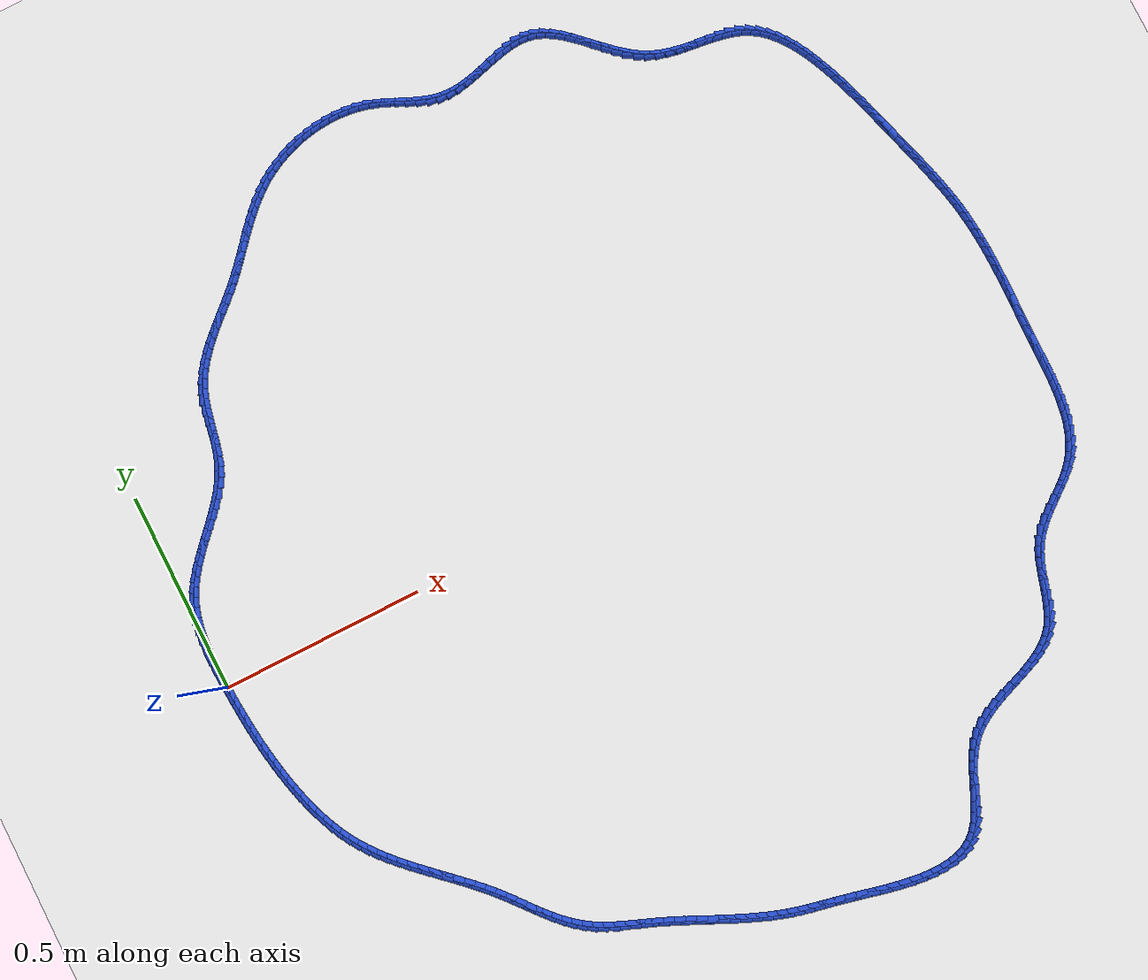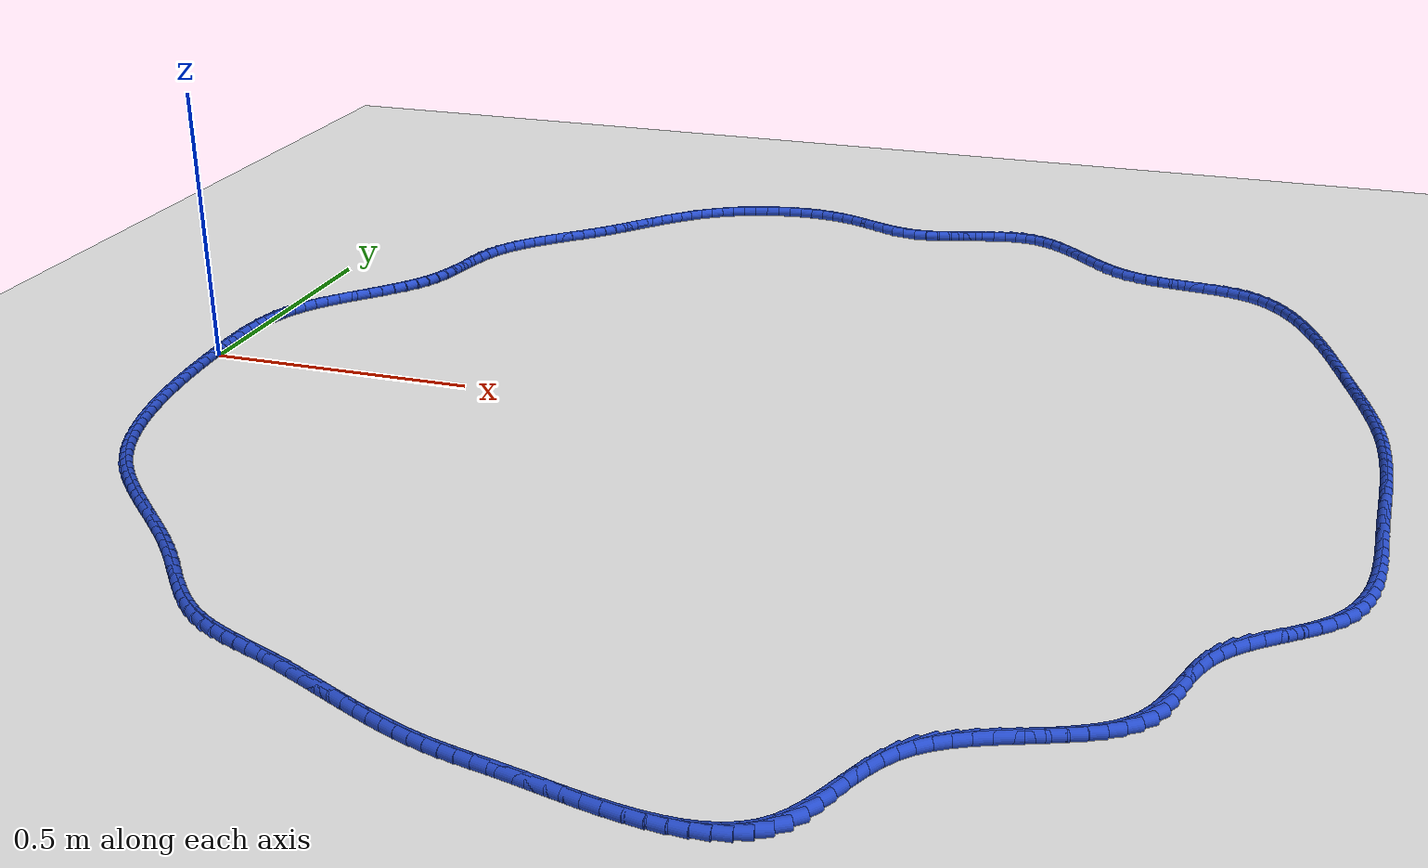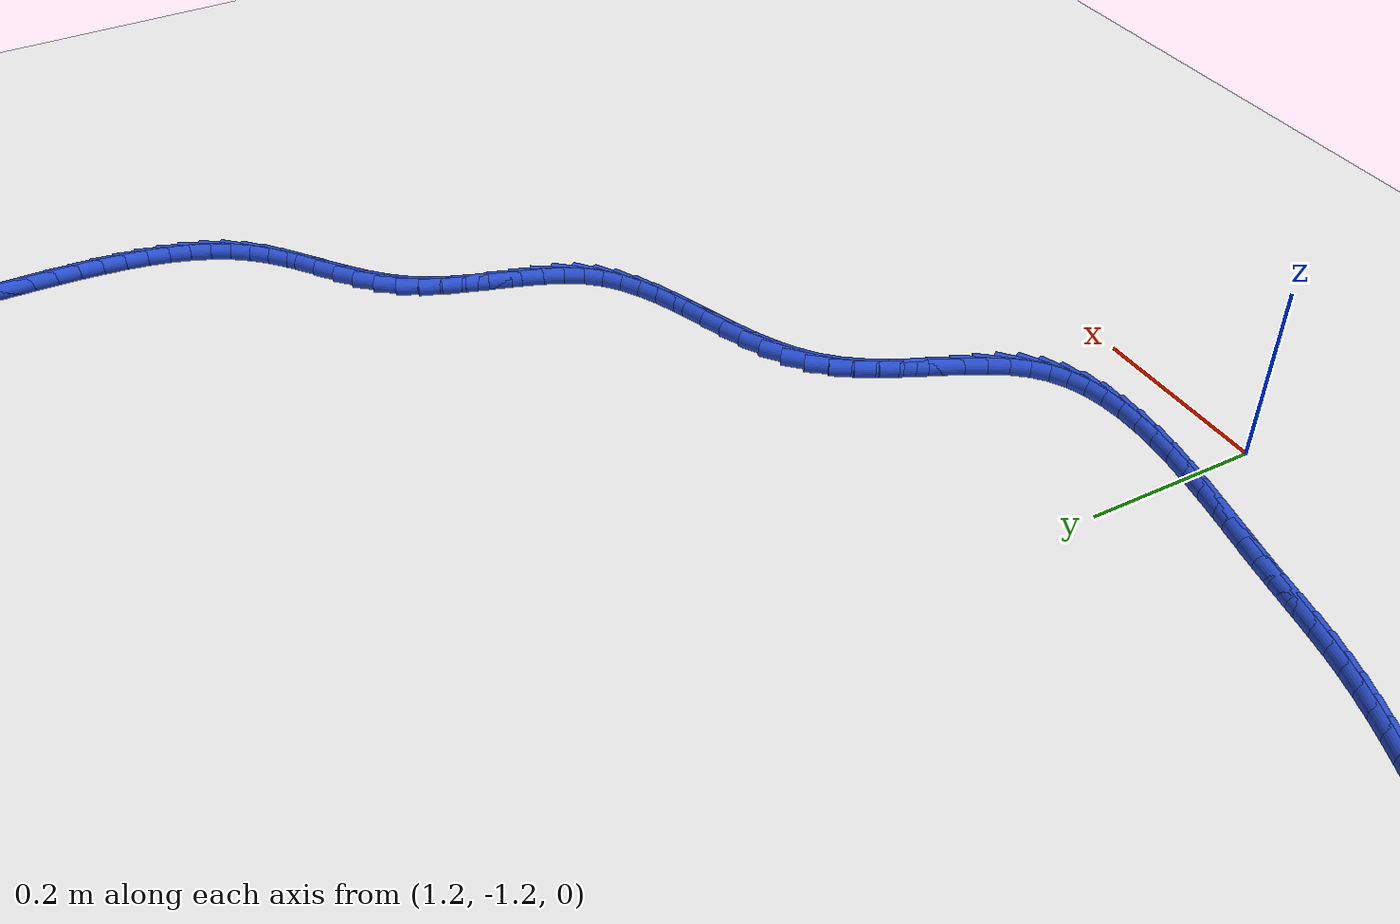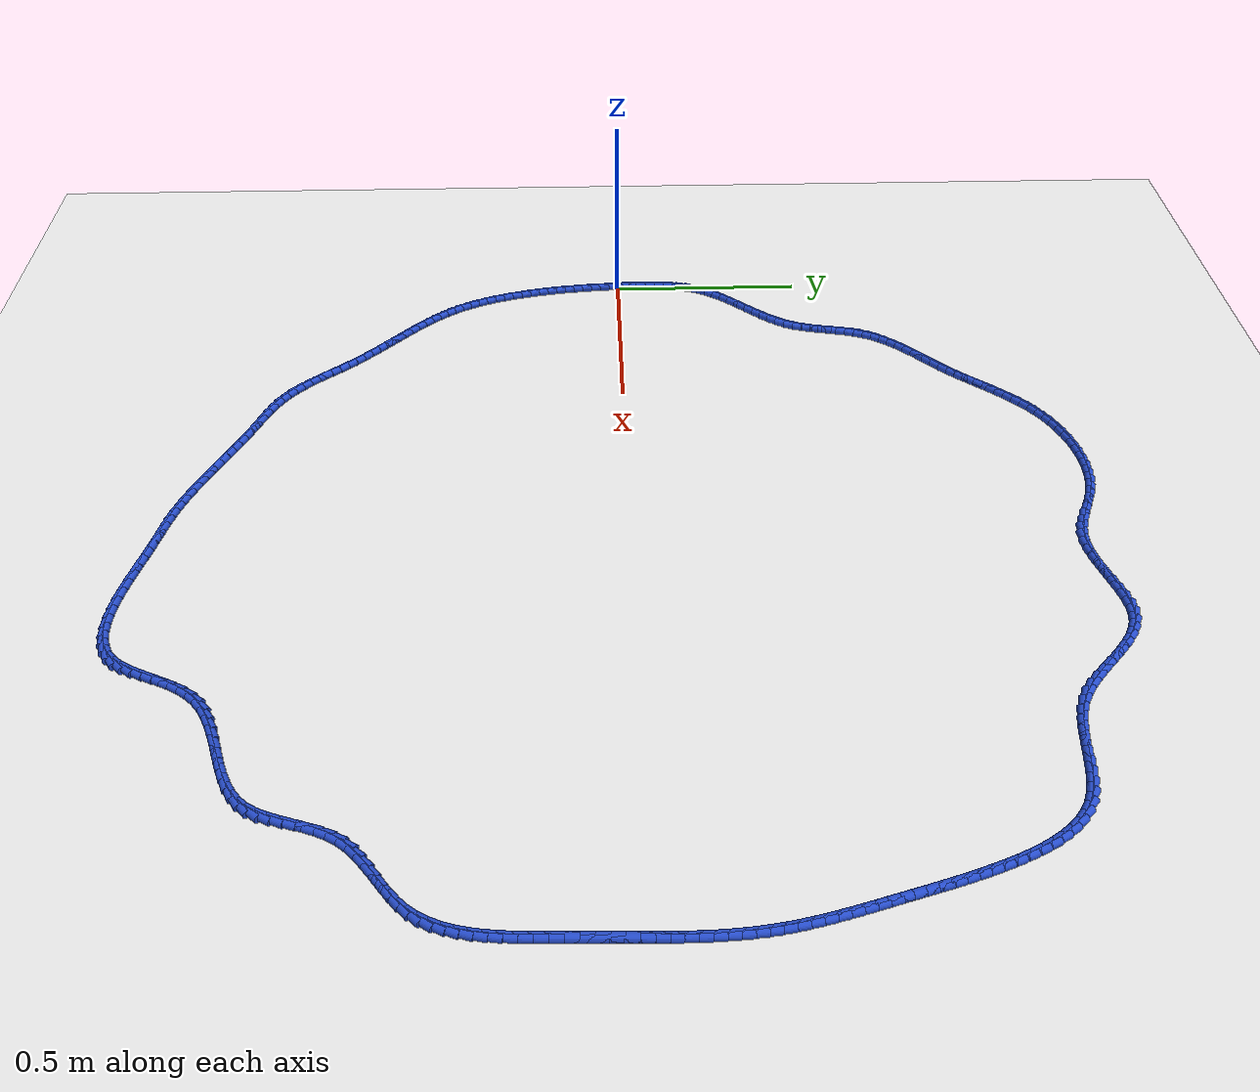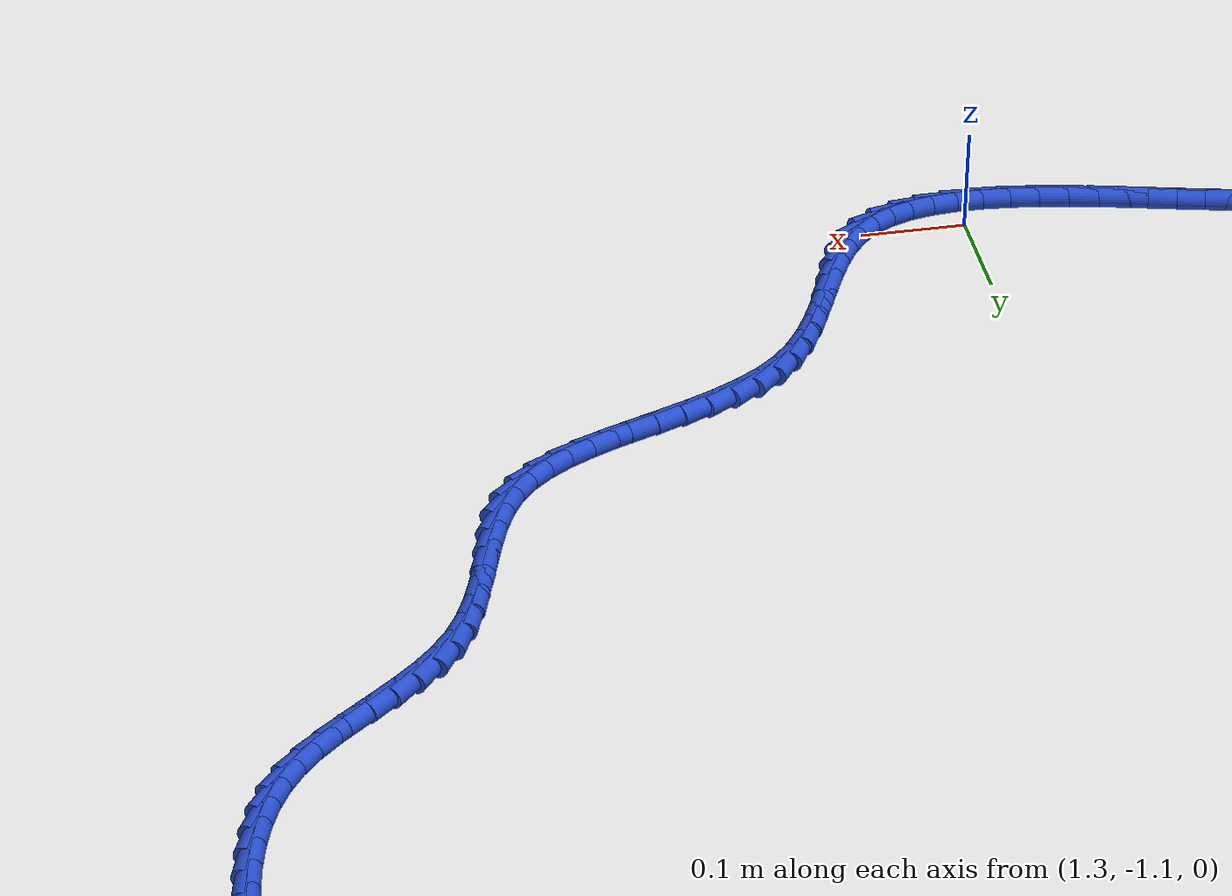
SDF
<sdf version="1.6">
 <world name="default">
  <light name="sun" type="directional">
   <pose>0 0 10 0 -0 0</pose>
   <diffuse>0.8 0.8 0.8 1</diffuse>
   <specular>0.2 0.2 0.2 1</specular>
   <attenuation>
    <range>1000</range>
    <constant>0.9</constant>
    <linear>0.01</linear>
    <quadratic>0.001</quadratic>
   </attenuation>
   <direction>-0.5 0.1 -0.9</direction>
  </light>
  <model name="ground_plane">
   <static>1</static>
   <link name="link">
    <collision name="collision">
     <geometry><plane><normal>0 0 1</normal><size>100 100</size></plane></geometry>
     <surface><friction><ode><mu>100</mu><mu2>50</mu2></ode></friction></surface>
    </collision>
    <visual name="visual">
     <cast_shadows>0</cast_shadows>
     <geometry><plane><normal>0 0 1</normal><size>100 100</size></plane></geometry>
     <material>
      <script><uri>file://media/materials/scripts/gazebo.material</uri><name>Gazebo/WhiteGlow</name></script>
     </material>
    </visual>
   </link>
  </model>
  <gravity>0 0 -9.8</gravity>
  <magnetic_field>6e-06 2.3e-05 -4.2e-05</magnetic_field>
  <atmosphere type="adiabatic"/>
  <physics name="default_physics" default="0" type="ode">
   <max_step_size>0.001</max_step_size>
   <real_time_factor>1</real_time_factor>
   <real_time_update_rate>1000</real_time_update_rate>
  </physics>
  <scene><ambient>0.4 0.4 0.4 1</ambient><background>0.7 0.7 0.7 1</background><shadows>1</shadows></scene>
  <spherical_coordinates>
   <surface_model>EARTH_WGS84</surface_model>
   <latitude_deg>0</latitude_deg>
   <longitude_deg>0</longitude_deg>
   <elevation>0</elevation>
   <heading_deg>0</heading_deg>
  </spherical_coordinates>
  <model name="line">
   <link name="link_0">
    <pose>-9.75781955236954e-18 -6.938893903907228e-18 0.01 0 1.57 -1.5243373193202743</pose>
    <collision name="collision">
     <geometry><cylinder><radius>0.01</radius><length>0.08</length></cylinder></geometry>
    </collision>
    <visual name="visual">
     <material>
      <script><name>Gazebo/Blue</name><uri>file://media/materials/scripts/gazebo.material</uri></script>
     </material>
     <geometry><cylinder><radius>0.01</radius><length>0.08</length></cylinder></geometry>
    </visual>
   </link>
   <link name="link_1">
    <pose>-0.0012050888104080423 0.02592008986052021 0.01 0 1.57 -1.5419578158329121</pose>
    <collision name="collision">
     <geometry><cylinder><radius>0.01</radius><length>0.08</length></cylinder></geometry>
    </collision>
    <visual name="visual">
     <material>
      <script><name>Gazebo/Blue</name><uri>file://media/materials/scripts/gazebo.material</uri></script>
     </material>
     <geometry><cylinder><radius>0.01</radius><length>0.08</length></cylinder></geometry>
    </visual>
   </link>
   <link name="link_2">
    <pose>-0.0019567881577833793 0.0519786804302538 0.01 0 1.57 -1.568173875574855</pose>
    <collision name="collision">
     <geometry><cylinder><radius>0.01</radius><length>0.08</length></cylinder></geometry>
    </collision>
    <visual name="visual">
     <material>
      <script><name>Gazebo/Blue</name><uri>file://media/materials/scripts/gazebo.material</uri></script>
     </material>
     <geometry><cylinder><radius>0.01</radius><length>0.08</length></cylinder></geometry>
    </visual>
   </link>
   <link name="link_3">
    <pose>-0.0020251028692053895 0.0780285662371162 0.01 0 1.57 1.5381723187275815</pose>
    <collision name="collision">
     <geometry><cylinder><radius>0.01</radius><length>0.08</length></cylinder></geometry>
    </collision>
    <visual name="visual">
     <material>
      <script><name>Gazebo/Blue</name><uri>file://media/materials/scripts/gazebo.material</uri></script>
     </material>
     <geometry><cylinder><radius>0.01</radius><length>0.08</length></cylinder></geometry>
    </visual>
   </link>
   <link name="link_4">
    <pose>-0.0011800377717534442 0.1039225418090228 0.01 0 1.57 1.4932509529633828</pose>
    <collision name="collision">
     <geometry><cylinder><radius>0.01</radius><length>0.08</length></cylinder></geometry>
    </collision>
    <visual name="visual">
     <material>
      <script><name>Gazebo/Blue</name><uri>file://media/materials/scripts/gazebo.material</uri></script>
     </material>
     <geometry><cylinder><radius>0.01</radius><length>0.08</length></cylinder></geometry>
    </visual>
   </link>
   <link name="link_5">
    <pose>0.000808402307493088 0.12951340167388908 0.01 0 1.57 1.4378642211099277</pose>
    <collision name="collision">
     <geometry><cylinder><radius>0.01</radius><length>0.08</length></cylinder></geometry>
    </collision>
    <visual name="visual">
     <material>
      <script><name>Gazebo/Blue</name><uri>file://media/materials/scripts/gazebo.material</uri></script>
     </material>
     <geometry><cylinder><radius>0.01</radius><length>0.08</length></cylinder></geometry>
    </visual>
   </link>
   <link name="link_6">
    <pose>0.0041702125414548406 0.15465394035963057 0.01 0 1.57 1.3711853472361413</pose>
    <collision name="collision">
     <geometry><cylinder><radius>0.01</radius><length>0.08</length></cylinder></geometry>
    </collision>
    <visual name="visual">
     <material>
      <script><name>Gazebo/Blue</name><uri>file://media/materials/scripts/gazebo.material</uri></script>
     </material>
     <geometry><cylinder><radius>0.01</radius><length>0.08</length></cylinder></geometry>
    </visual>
   </link>
   <link name="link_7">
    <pose>0.009135388103052438 0.1791969523941626 0.01 0 1.57 1.2925344477726048</pose>
    <collision name="collision">
     <geometry><cylinder><radius>0.01</radius><length>0.08</length></cylinder></geometry>
    </collision>
    <visual name="visual">
     <material>
      <script><name>Gazebo/Blue</name><uri>file://media/materials/scripts/gazebo.material</uri></script>
     </material>
     <geometry><cylinder><radius>0.01</radius><length>0.08</length></cylinder></geometry>
    </visual>
   </link>
   <link name="link_8">
    <pose>0.015933924165206503 0.20299523230540073 0.01 0 1.57 1.2016555358553467</pose>
    <collision name="collision">
     <geometry><cylinder><radius>0.01</radius><length>0.08</length></cylinder></geometry>
    </collision>
    <visual name="visual">
     <material>
      <script><name>Gazebo/Blue</name><uri>file://media/materials/scripts/gazebo.material</uri></script>
     </material>
     <geometry><cylinder><radius>0.01</radius><length>0.08</length></cylinder></geometry>
    </visual>
   </link>
   <link name="link_9">
    <pose>0.02479581590083768 0.2259015746212603 0.01 0 1.57 1.1014199126125375</pose>
    <collision name="collision">
     <geometry><cylinder><radius>0.01</radius><length>0.08</length></cylinder></geometry>
    </collision>
    <visual name="visual">
     <material>
      <script><name>Gazebo/Blue</name><uri>file://media/materials/scripts/gazebo.material</uri></script>
     </material>
     <geometry><cylinder><radius>0.01</radius><length>0.08</length></cylinder></geometry>
    </visual>
   </link>
   <link name="link_10">
    <pose>0.03590022369805859 0.24779591496566802 0.01 0 1.57 1.011174494806404</pose>
    <collision name="collision">
     <geometry><cylinder><radius>0.01</radius><length>0.08</length></cylinder></geometry>
    </collision>
    <visual name="visual">
     <material>
      <script><name>Gazebo/Blue</name><uri>file://media/materials/scripts/gazebo.material</uri></script>
     </material>
     <geometry><cylinder><radius>0.01</radius><length>0.08</length></cylinder></geometry>
    </visual>
   </link>
   <link name="link_11">
    <pose>0.049036543903759285 0.26876628708482003 0.01 0 1.57 0.9399334317003115</pose>
    <collision name="collision">
     <geometry><cylinder><radius>0.01</radius><length>0.08</length></cylinder></geometry>
    </collision>
    <visual name="visual">
     <material>
      <script><name>Gazebo/Blue</name><uri>file://media/materials/scripts/gazebo.material</uri></script>
     </material>
     <geometry><cylinder><radius>0.01</radius><length>0.08</length></cylinder></geometry>
    </visual>
   </link>
   <link name="link_12">
    <pose>0.0638138206214321 0.2889970162224054 0.01 0 1.57 0.8872686179507671</pose>
    <collision name="collision">
     <geometry><cylinder><radius>0.01</radius><length>0.08</length></cylinder></geometry>
    </collision>
    <visual name="visual">
     <material>
      <script><name>Gazebo/Blue</name><uri>file://media/materials/scripts/gazebo.material</uri></script>
     </material>
     <geometry><cylinder><radius>0.01</radius><length>0.08</length></cylinder></geometry>
    </visual>
   </link>
   <link name="link_13">
    <pose>0.07984011867928323 0.30867295046497906 0.01 0 1.57 0.8522408303125061</pose>
    <collision name="collision">
     <geometry><cylinder><radius>0.01</radius><length>0.08</length></cylinder></geometry>
    </collision>
    <visual name="visual">
     <material>
      <script><name>Gazebo/Blue</name><uri>file://media/materials/scripts/gazebo.material</uri></script>
     </material>
     <geometry><cylinder><radius>0.01</radius><length>0.08</length></cylinder></geometry>
    </visual>
   </link>
   <link name="link_14">
    <pose>0.09672350290551884 0.3279789378990955 0.01 0 1.57 0.8339582983865975</pose>
    <collision name="collision">
     <geometry><cylinder><radius>0.01</radius><length>0.08</length></cylinder></geometry>
    </collision>
    <visual name="visual">
     <material>
      <script><name>Gazebo/Blue</name><uri>file://media/materials/scripts/gazebo.material</uri></script>
     </material>
     <geometry><cylinder><radius>0.01</radius><length>0.08</length></cylinder></geometry>
    </visual>
   </link>
   <link name="link_15">
    <pose>0.11407203812834507 0.34709982661130934 0.01 0 1.57 0.8318555698062247</pose>
    <collision name="collision">
     <geometry><cylinder><radius>0.01</radius><length>0.08</length></cylinder></geometry>
    </collision>
    <visual name="visual">
     <material>
      <script><name>Gazebo/Blue</name><uri>file://media/materials/scripts/gazebo.material</uri></script>
     </material>
     <geometry><cylinder><radius>0.01</radius><length>0.08</length></cylinder></geometry>
    </visual>
   </link>
   <link name="link_16">
    <pose>0.13149378917596807 0.3662204646881755 0.01 0 1.57 0.8458109271327214</pose>
    <collision name="collision">
     <geometry><cylinder><radius>0.01</radius><length>0.08</length></cylinder></geometry>
    </collision>
    <visual name="visual">
     <material>
      <script><name>Gazebo/Blue</name><uri>file://media/materials/scripts/gazebo.material</uri></script>
     </material>
     <geometry><cylinder><radius>0.01</radius><length>0.08</length></cylinder></geometry>
    </visual>
   </link>
   <link name="link_17">
    <pose>0.1485968208765941 0.38552570021624855 0.01 0 1.57 0.8761537570166438</pose>
    <collision name="collision">
     <geometry><cylinder><radius>0.01</radius><length>0.08</length></cylinder></geometry>
    </collision>
    <visual name="visual">
     <material>
      <script><name>Gazebo/Blue</name><uri>file://media/materials/scripts/gazebo.material</uri></script>
     </material>
     <geometry><cylinder><radius>0.01</radius><length>0.08</length></cylinder></geometry>
    </visual>
   </link>
   <link name="link_18">
    <pose>0.16498919805842915 0.405200381282083 0.01 0 1.57 0.9235706233107076</pose>
    <collision name="collision">
     <geometry><cylinder><radius>0.01</radius><length>0.08</length></cylinder></geometry>
    </collision>
    <visual name="visual">
     <material>
      <script><name>Gazebo/Blue</name><uri>file://media/materials/scripts/gazebo.material</uri></script>
     </material>
     <geometry><cylinder><radius>0.01</radius><length>0.08</length></cylinder></geometry>
    </visual>
   </link>
   <link name="link_19">
    <pose>0.1802789855496796 0.4254293559722342 0.01 0 1.57 0.988876256986188</pose>
    <collision name="collision">
     <geometry><cylinder><radius>0.01</radius><length>0.08</length></cylinder></geometry>
    </collision>
    <visual name="visual">
     <material>
      <script><name>Gazebo/Blue</name><uri>file://media/materials/scripts/gazebo.material</uri></script>
     </material>
     <geometry><cylinder><radius>0.01</radius><length>0.08</length></cylinder></geometry>
    </visual>
   </link>
   <link name="link_20">
    <pose>0.1940742481785515 0.4463974723732562 0.01 0 1.57 1.0725890455710496</pose>
    <collision name="collision">
     <geometry><cylinder><radius>0.01</radius><length>0.08</length></cylinder></geometry>
    </collision>
    <visual name="visual">
     <material>
      <script><name>Gazebo/Blue</name><uri>file://media/materials/scripts/gazebo.material</uri></script>
     </material>
     <geometry><cylinder><radius>0.01</radius><length>0.08</length></cylinder></geometry>
    </visual>
   </link>
   <link name="link_21">
    <pose>0.20598305077325105 0.46828957857170406 0.01 0 1.57 1.1731129228180945</pose>
    <collision name="collision">
     <geometry><cylinder><radius>0.01</radius><length>0.08</length></cylinder></geometry>
    </collision>
    <visual name="visual">
     <material>
      <script><name>Gazebo/Blue</name><uri>file://media/materials/scripts/gazebo.material</uri></script>
     </material>
     <geometry><cylinder><radius>0.01</radius><length>0.08</length></cylinder></geometry>
    </visual>
   </link>
   <link name="link_22">
    <pose>0.21563951747753632 0.4912775979634214 0.01 0 1.57 1.2659504119125033</pose>
    <collision name="collision">
     <geometry><cylinder><radius>0.01</radius><length>0.08</length></cylinder></geometry>
    </collision>
    <visual name="visual">
     <material>
      <script><name>Gazebo/Blue</name><uri>file://media/materials/scripts/gazebo.material</uri></script>
     </material>
     <geometry><cylinder><radius>0.01</radius><length>0.08</length></cylinder></geometry>
    </visual>
   </link>
   <link name="link_23">
    <pose>0.22319153853211807 0.515278640348412 0.01 0 1.57 1.3299655675442235</pose>
    <collision name="collision">
     <geometry><cylinder><radius>0.01</radius><length>0.08</length></cylinder></geometry>
    </collision>
    <visual name="visual">
     <material>
      <script><name>Gazebo/Blue</name><uri>file://media/materials/scripts/gazebo.material</uri></script>
     </material>
     <geometry><cylinder><radius>0.01</radius><length>0.08</length></cylinder></geometry>
    </visual>
   </link>
   <link name="link_24">
    <pose>0.22925728544944848 0.5399765691863327 0.01 0 1.57 1.3657047859916154</pose>
    <collision name="collision">
     <geometry><cylinder><radius>0.01</radius><length>0.08</length></cylinder></geometry>
    </collision>
    <visual name="visual">
     <material>
      <script><name>Gazebo/Blue</name><uri>file://media/materials/scripts/gazebo.material</uri></script>
     </material>
     <geometry><cylinder><radius>0.01</radius><length>0.08</length></cylinder></geometry>
    </visual>
   </link>
   <link name="link_25">
    <pose>0.2344722707640014 0.5650466472755613 0.01 0 1.57 1.3743105719394462</pose>
    <collision name="collision">
     <geometry><cylinder><radius>0.01</radius><length>0.08</length></cylinder></geometry>
    </collision>
    <visual name="visual">
     <material>
      <script><name>Gazebo/Blue</name><uri>file://media/materials/scripts/gazebo.material</uri></script>
     </material>
     <geometry><cylinder><radius>0.01</radius><length>0.08</length></cylinder></geometry>
    </visual>
   </link>
   <link name="link_26">
    <pose>0.2394720070102504 0.5901641374144748 0.01 0 1.57 1.355968346934013</pose>
    <collision name="collision">
     <geometry><cylinder><radius>0.01</radius><length>0.08</length></cylinder></geometry>
    </collision>
    <visual name="visual">
     <material>
      <script><name>Gazebo/Blue</name><uri>file://media/materials/scripts/gazebo.material</uri></script>
     </material>
     <geometry><cylinder><radius>0.01</radius><length>0.08</length></cylinder></geometry>
    </visual>
   </link>
   <link name="link_27">
    <pose>0.24489200672266925 0.6150043024014505 0.01 0 1.57 1.3097209256946942</pose>
    <collision name="collision">
     <geometry><cylinder><radius>0.01</radius><length>0.08</length></cylinder></geometry>
    </collision>
    <visual name="visual">
     <material>
      <script><name>Gazebo/Blue</name><uri>file://media/materials/scripts/gazebo.material</uri></script>
     </material>
     <geometry><cylinder><radius>0.01</radius><length>0.08</length></cylinder></geometry>
    </visual>
   </link>
   <link name="link_28">
    <pose>0.2513677824357316 0.6392424050348656 0.01 0 1.57 1.2338116778294277</pose>
    <collision name="collision">
     <geometry><cylinder><radius>0.01</radius><length>0.08</length></cylinder></geometry>
    </collision>
    <visual name="visual">
     <material>
      <script><name>Gazebo/Blue</name><uri>file://media/materials/scripts/gazebo.material</uri></script>
     </material>
     <geometry><cylinder><radius>0.01</radius><length>0.08</length></cylinder></geometry>
    </visual>
   </link>
   <link name="link_29">
    <pose>0.25953484668391136 0.6625537081130977 0.01 0 1.57 1.1310199491851476</pose>
    <collision name="collision">
     <geometry><cylinder><radius>0.01</radius><length>0.08</length></cylinder></geometry>
    </collision>
    <visual name="visual">
     <material>
      <script><name>Gazebo/Blue</name><uri>file://media/materials/scripts/gazebo.material</uri></script>
     </material>
     <geometry><cylinder><radius>0.01</radius><length>0.08</length></cylinder></geometry>
    </visual>
   </link>
   <link name="link_30">
    <pose>0.2699370110502156 0.6846621064124442 0.01 0 1.57 1.0303191824166575</pose>
    <collision name="collision">
     <geometry><cylinder><radius>0.01</radius><length>0.08</length></cylinder></geometry>
    </collision>
    <visual name="visual">
     <material>
      <script><name>Gazebo/Blue</name><uri>file://media/materials/scripts/gazebo.material</uri></script>
     </material>
     <geometry><cylinder><radius>0.01</radius><length>0.08</length></cylinder></geometry>
    </visual>
   </link>
   <link name="link_31">
    <pose>0.2825098327904892 0.7056140716349091 0.01 0 1.57 0.9451063912808295</pose>
    <collision name="collision">
     <geometry><cylinder><radius>0.01</radius><length>0.08</length></cylinder></geometry>
    </collision>
    <visual name="visual">
     <material>
      <script><name>Gazebo/Blue</name><uri>file://media/materials/scripts/gazebo.material</uri></script>
     </material>
     <geometry><cylinder><radius>0.01</radius><length>0.08</length></cylinder></geometry>
    </visual>
   </link>
   <link name="link_32">
    <pose>0.29694124236754105 0.7255873999730142 0.01 0 1.57 0.8760637971794023</pose>
    <collision name="collision">
     <geometry><cylinder><radius>0.01</radius><length>0.08</length></cylinder></geometry>
    </collision>
    <visual name="visual">
     <material>
      <script><name>Gazebo/Blue</name><uri>file://media/materials/scripts/gazebo.material</uri></script>
     </material>
     <geometry><cylinder><radius>0.01</radius><length>0.08</length></cylinder></geometry>
    </visual>
   </link>
   <link name="link_33">
    <pose>0.3129184479354378 0.7447602706829499 0.01 0 1.57 0.8228625204332671</pose>
    <collision name="collision">
     <geometry><cylinder><radius>0.01</radius><length>0.08</length></cylinder></geometry>
    </collision>
    <visual name="visual">
     <material>
      <script><name>Gazebo/Blue</name><uri>file://media/materials/scripts/gazebo.material</uri></script>
     </material>
     <geometry><cylinder><radius>0.01</radius><length>0.08</length></cylinder></geometry>
    </visual>
   </link>
   <link name="link_34">
    <pose>0.33012865764824617 0.763310863020906 0.01 0 1.57 0.7847378205954241</pose>
    <collision name="collision">
     <geometry><cylinder><radius>0.01</radius><length>0.08</length></cylinder></geometry>
    </collision>
    <visual name="visual">
     <material>
      <script><name>Gazebo/Blue</name><uri>file://media/materials/scripts/gazebo.material</uri></script>
     </material>
     <geometry><cylinder><radius>0.01</radius><length>0.08</length></cylinder></geometry>
    </visual>
   </link>
   <link name="link_35">
    <pose>0.3482590796600325 0.781417356243072 0.01 0 1.57 0.7608730663376072</pose>
    <collision name="collision">
     <geometry><cylinder><radius>0.01</radius><length>0.08</length></cylinder></geometry>
    </collision>
    <visual name="visual">
     <material>
      <script><name>Gazebo/Blue</name><uri>file://media/materials/scripts/gazebo.material</uri></script>
     </material>
     <geometry><cylinder><radius>0.01</radius><length>0.08</length></cylinder></geometry>
    </visual>
   </link>
   <link name="link_36">
    <pose>0.3669969221248638 0.7992579296056385 0.01 0 1.57 0.7506255127676112</pose>
    <collision name="collision">
     <geometry><cylinder><radius>0.01</radius><length>0.08</length></cylinder></geometry>
    </collision>
    <visual name="visual">
     <material>
      <script><name>Gazebo/Blue</name><uri>file://media/materials/scripts/gazebo.material</uri></script>
     </material>
     <geometry><cylinder><radius>0.01</radius><length>0.08</length></cylinder></geometry>
    </visual>
   </link>
   <link name="link_37">
    <pose>0.38602939319680657 0.8170107623647951 0.01 0 1.57 0.7536369178883096</pose>
    <collision name="collision">
     <geometry><cylinder><radius>0.01</radius><length>0.08</length></cylinder></geometry>
    </collision>
    <visual name="visual">
     <material>
      <script><name>Gazebo/Blue</name><uri>file://media/materials/scripts/gazebo.material</uri></script>
     </material>
     <geometry><cylinder><radius>0.01</radius><length>0.08</length></cylinder></geometry>
    </visual>
   </link>
   <link name="link_38">
    <pose>0.40504370102992737 0.8348540337767315 0.01 0 1.57 0.7698685064474259</pose>
    <collision name="collision">
     <geometry><cylinder><radius>0.01</radius><length>0.08</length></cylinder></geometry>
    </collision>
    <visual name="visual">
     <material>
      <script><name>Gazebo/Blue</name><uri>file://media/materials/scripts/gazebo.material</uri></script>
     </material>
     <geometry><cylinder><radius>0.01</radius><length>0.08</length></cylinder></geometry>
    </visual>
   </link>
   <link name="link_39">
    <pose>0.4237270537782928 0.8529659230976379 0.01 0 1.57 0.7989882519980893</pose>
    <collision name="collision">
     <geometry><cylinder><radius>0.01</radius><length>0.08</length></cylinder></geometry>
    </collision>
    <visual name="visual">
     <material>
      <script><name>Gazebo/Blue</name><uri>file://media/materials/scripts/gazebo.material</uri></script>
     </material>
     <geometry><cylinder><radius>0.01</radius><length>0.08</length></cylinder></geometry>
    </visual>
   </link>
   <link name="link_40">
    <pose>0.4417794189299816 0.8715157458515507 0.01 0 1.57 0.8294605872397544</pose>
    <collision name="collision">
     <geometry><cylinder><radius>0.01</radius><length>0.08</length></cylinder></geometry>
    </collision>
    <visual name="visual">
     <material>
      <script><name>Gazebo/Blue</name><uri>file://media/materials/scripts/gazebo.material</uri></script>
     </material>
     <geometry><cylinder><radius>0.01</radius><length>0.08</length></cylinder></geometry>
    </visual>
   </link>
   <link name="link_41">
    <pose>0.4591561144824855 0.8904954291095858 0.01 0 1.57 0.8502257027616947</pose>
    <collision name="collision">
     <geometry><cylinder><radius>0.01</radius><length>0.08</length></cylinder></geometry>
    </collision>
    <visual name="visual">
     <material>
      <script><name>Gazebo/Blue</name><uri>file://media/materials/scripts/gazebo.material</uri></script>
     </material>
     <geometry><cylinder><radius>0.01</radius><length>0.08</length></cylinder></geometry>
    </visual>
   </link>
   <link name="link_42">
    <pose>0.4760482740108255 0.9097330821358439 0.01 0 1.57 0.8606897198877618</pose>
    <collision name="collision">
     <geometry><cylinder><radius>0.01</radius><length>0.08</length></cylinder></geometry>
    </collision>
    <visual name="visual">
     <material>
      <script><name>Gazebo/Blue</name><uri>file://media/materials/scripts/gazebo.material</uri></script>
     </material>
     <geometry><cylinder><radius>0.01</radius><length>0.08</length></cylinder></geometry>
    </visual>
   </link>
   <link name="link_43">
    <pose>0.4926558756782397 0.9290506699818125 0.01 0 1.57 0.860696949263899</pose>
    <collision name="collision">
     <geometry><cylinder><radius>0.01</radius><length>0.08</length></cylinder></geometry>
    </collision>
    <visual name="visual">
     <material>
      <script><name>Gazebo/Blue</name><uri>file://media/materials/scripts/gazebo.material</uri></script>
     </material>
     <geometry><cylinder><radius>0.01</radius><length>0.08</length></cylinder></geometry>
    </visual>
   </link>
   <link name="link_44">
    <pose>0.5091788976479665 0.9482701576989787 0.01 0 1.57 0.8500862347424606</pose>
    <collision name="collision">
     <geometry><cylinder><radius>0.01</radius><length>0.08</length></cylinder></geometry>
    </collision>
    <visual name="visual">
     <material>
      <script><name>Gazebo/Blue</name><uri>file://media/materials/scripts/gazebo.material</uri></script>
     </material>
     <geometry><cylinder><radius>0.01</radius><length>0.08</length></cylinder></geometry>
    </visual>
   </link>
   <link name="link_45">
    <pose>0.5258173180832444 0.9672135103388305 0.01 0 1.57 0.8286909735105473</pose>
    <collision name="collision">
     <geometry><cylinder><radius>0.01</radius><length>0.08</length></cylinder></geometry>
    </collision>
    <visual name="visual">
     <material>
      <script><name>Gazebo/Blue</name><uri>file://media/materials/scripts/gazebo.material</uri></script>
     </material>
     <geometry><cylinder><radius>0.01</radius><length>0.08</length></cylinder></geometry>
    </visual>
   </link>
   <link name="link_46">
    <pose>0.5427711151473117 0.985702692952855 0.01 0 1.57 0.7963761620971073</pose>
    <collision name="collision">
     <geometry><cylinder><radius>0.01</radius><length>0.08</length></cylinder></geometry>
    </collision>
    <visual name="visual">
     <material>
      <script><name>Gazebo/Blue</name><uri>file://media/materials/scripts/gazebo.material</uri></script>
     </material>
     <geometry><cylinder><radius>0.01</radius><length>0.08</length></cylinder></geometry>
    </visual>
   </link>
   <link name="link_47">
    <pose>0.5602402670034067 1.00355967059254 0.01 0 1.57 0.7531156665826948</pose>
    <collision name="collision">
     <geometry><cylinder><radius>0.01</radius><length>0.08</length></cylinder></geometry>
    </collision>
    <visual name="visual">
     <material>
      <script><name>Gazebo/Blue</name><uri>file://media/materials/scripts/gazebo.material</uri></script>
     </material>
     <geometry><cylinder><radius>0.01</radius><length>0.08</length></cylinder></geometry>
    </visual>
   </link>
   <link name="link_48">
    <pose>0.5784247518147678 1.0206064083093729 0.01 0 1.57 0.6991088813412948</pose>
    <collision name="collision">
     <geometry><cylinder><radius>0.01</radius><length>0.08</length></cylinder></geometry>
    </collision>
    <visual name="visual">
     <material>
      <script><name>Gazebo/Blue</name><uri>file://media/materials/scripts/gazebo.material</uri></script>
     </material>
     <geometry><cylinder><radius>0.01</radius><length>0.08</length></cylinder></geometry>
    </visual>
   </link>
   <link name="link_49">
    <pose>0.5975245477446336 1.0366648711548414 0.01 0 1.57 0.6349250009315921</pose>
    <collision name="collision">
     <geometry><cylinder><radius>0.01</radius><length>0.08</length></cylinder></geometry>
    </collision>
    <visual name="visual">
     <material>
      <script><name>Gazebo/Blue</name><uri>file://media/materials/scripts/gazebo.material</uri></script>
     </material>
     <geometry><cylinder><radius>0.01</radius><length>0.08</length></cylinder></geometry>
    </visual>
   </link>
   <link name="link_50">
    <pose>0.6177396329562421 1.051557024180433 0.01 0 1.57 0.5632501137522673</pose>
    <collision name="collision">
     <geometry><cylinder><radius>0.01</radius><length>0.08</length></cylinder></geometry>
    </collision>
    <visual name="visual">
     <material>
      <script><name>Gazebo/Blue</name><uri>file://media/materials/scripts/gazebo.material</uri></script>
     </material>
     <geometry><cylinder><radius>0.01</radius><length>0.08</length></cylinder></geometry>
    </visual>
   </link>
   <link name="link_51">
    <pose>0.6392177955682968 1.0651201921469313 0.01 0 1.57 0.49220218962726064</pose>
    <collision name="collision">
     <geometry><cylinder><radius>0.01</radius><length>0.08</length></cylinder></geometry>
    </collision>
    <visual name="visual">
     <material>
      <script><name>Gazebo/Blue</name><uri>file://media/materials/scripts/gazebo.material</uri></script>
     </material>
     <geometry><cylinder><radius>0.01</radius><length>0.08</length></cylinder></geometry>
    </visual>
   </link>
   <link name="link_52">
    <pose>0.6618635416380242 1.0772632985610977 0.01 0 1.57 0.4232640055669498</pose>
    <collision name="collision">
     <geometry><cylinder><radius>0.01</radius><length>0.08</length></cylinder></geometry>
    </collision>
    <visual name="visual">
     <material>
      <script><name>Gazebo/Blue</name><uri>file://media/materials/scripts/gazebo.material</uri></script>
     </material>
     <geometry><cylinder><radius>0.01</radius><length>0.08</length></cylinder></geometry>
    </visual>
   </link>
   <link name="link_53">
    <pose>0.6855105450625127 1.087916113077618 0.01 0 1.57 0.3556002629308807</pose>
    <collision name="collision">
     <geometry><cylinder><radius>0.01</radius><length>0.08</length></cylinder></geometry>
    </collision>
    <visual name="visual">
     <material>
      <script><name>Gazebo/Blue</name><uri>file://media/materials/scripts/gazebo.material</uri></script>
     </material>
     <geometry><cylinder><radius>0.01</radius><length>0.08</length></cylinder></geometry>
    </visual>
   </link>
   <link name="link_54">
    <pose>0.7099924716709883 1.0970084077255775 0.01 0 1.57 0.2884041937840545</pose>
    <collision name="collision">
     <geometry><cylinder><radius>0.01</radius><length>0.08</length></cylinder></geometry>
    </collision>
    <visual name="visual">
     <material>
      <script><name>Gazebo/Blue</name><uri>file://media/materials/scripts/gazebo.material</uri></script>
     </material>
     <geometry><cylinder><radius>0.01</radius><length>0.08</length></cylinder></geometry>
    </visual>
   </link>
   <link name="link_55">
    <pose>0.7351429872926771 1.1044699545340617 0.01 0 1.57 0.22089504281320152</pose>
    <collision name="collision">
     <geometry><cylinder><radius>0.01</radius><length>0.08</length></cylinder></geometry>
    </collision>
    <visual name="visual">
     <material>
      <script><name>Gazebo/Blue</name><uri>file://media/materials/scripts/gazebo.material</uri></script>
     </material>
     <geometry><cylinder><radius>0.01</radius><length>0.08</length></cylinder></geometry>
    </visual>
   </link>
   <link name="link_56">
    <pose>0.7607957577568049 1.1102305255321552 0.01 0 1.57 0.15231503734382207</pose>
    <collision name="collision">
     <geometry><cylinder><radius>0.01</radius><length>0.08</length></cylinder></geometry>
    </collision>
    <visual name="visual">
     <material>
      <script><name>Gazebo/Blue</name><uri>file://media/materials/scripts/gazebo.material</uri></script>
     </material>
     <geometry><cylinder><radius>0.01</radius><length>0.08</length></cylinder></geometry>
    </visual>
   </link>
   <link name="link_57">
    <pose>0.7867844488925975 1.1142198927489433 0.01 0 1.57 0.08192922370429563</pose>
    <collision name="collision">
     <geometry><cylinder><radius>0.01</radius><length>0.08</length></cylinder></geometry>
    </collision>
    <visual name="visual">
     <material>
      <script><name>Gazebo/Blue</name><uri>file://media/materials/scripts/gazebo.material</uri></script>
     </material>
     <geometry><cylinder><radius>0.01</radius><length>0.08</length></cylinder></geometry>
    </visual>
   </link>
   <link name="link_58">
    <pose>0.812942726529281 1.116367828213511 0.01 0 1.57 0.009031173558403306</pose>
    <collision name="collision">
     <geometry><cylinder><radius>0.01</radius><length>0.08</length></cylinder></geometry>
    </collision>
    <visual name="visual">
     <material>
      <script><name>Gazebo/Blue</name><uri>file://media/materials/scripts/gazebo.material</uri></script>
     </material>
     <geometry><cylinder><radius>0.01</radius><length>0.08</length></cylinder></geometry>
    </visual>
   </link>
   <link name="link_59">
    <pose>0.839104256496082 1.1166041039549444 0.01 0 1.57 -0.06704230357622556</pose>
    <collision name="collision">
     <geometry><cylinder><radius>0.01</radius><length>0.08</length></cylinder></geometry>
    </collision>
    <visual name="visual">
     <material>
      <script><name>Gazebo/Blue</name><uri>file://media/materials/scripts/gazebo.material</uri></script>
     </material>
     <geometry><cylinder><radius>0.01</radius><length>0.08</length></cylinder></geometry>
    </visual>
   </link>
   <link name="link_60">
    <pose>0.8651027046222256 1.1148584920023281 0.01 0 1.57 -0.14688424052069246</pose>
    <collision name="collision">
     <geometry><cylinder><radius>0.01</radius><length>0.08</length></cylinder></geometry>
    </collision>
    <visual name="visual">
     <material>
      <script><name>Gazebo/Blue</name><uri>file://media/materials/scripts/gazebo.material</uri></script>
     </material>
     <geometry><cylinder><radius>0.01</radius><length>0.08</length></cylinder></geometry>
    </visual>
   </link>
   <link name="link_61">
    <pose>0.8907717367369385 1.1110607643847477 0.01 0 1.57 -0.23097571276008405</pose>
    <collision name="collision">
     <geometry><cylinder><radius>0.01</radius><length>0.08</length></cylinder></geometry>
    </collision>
    <visual name="visual">
     <material>
      <script><name>Gazebo/Blue</name><uri>file://media/materials/scripts/gazebo.material</uri></script>
     </material>
     <geometry><cylinder><radius>0.01</radius><length>0.08</length></cylinder></geometry>
    </visual>
   </link>
   <link name="link_62">
    <pose>0.9159450186694463 1.1051406931312875 0.01 0 1.57 -0.3174484262086904</pose>
    <collision name="collision">
     <geometry><cylinder><radius>0.01</radius><length>0.08</length></cylinder></geometry>
    </collision>
    <visual name="visual">
     <material>
      <script><name>Gazebo/Blue</name><uri>file://media/materials/scripts/gazebo.material</uri></script>
     </material>
     <geometry><cylinder><radius>0.01</radius><length>0.08</length></cylinder></geometry>
    </visual>
   </link>
   <link name="link_63">
    <pose>0.9404768165128634 1.0970805254697484 0.01 0 1.57 -0.3837631327545001</pose>
    <collision name="collision">
     <geometry><cylinder><radius>0.01</radius><length>0.08</length></cylinder></geometry>
    </collision>
    <visual name="visual">
     <material>
      <script><name>Gazebo/Blue</name><uri>file://media/materials/scripts/gazebo.material</uri></script>
     </material>
     <geometry><cylinder><radius>0.01</radius><length>0.08</length></cylinder></geometry>
    </visual>
   </link>
   <link name="link_64">
    <pose>0.9644350003025722 1.0874066234692479 0.01 0 1.57 -0.4167957000101921</pose>
    <collision name="collision">
     <geometry><cylinder><radius>0.01</radius><length>0.08</length></cylinder></geometry>
    </collision>
    <visual name="visual">
     <material>
      <script><name>Gazebo/Blue</name><uri>file://media/materials/scripts/gazebo.material</uri></script>
     </material>
     <geometry><cylinder><radius>0.01</radius><length>0.08</length></cylinder></geometry>
    </visual>
   </link>
   <link name="link_65">
    <pose>0.9880138815711068 1.0769674345238682 0.01 0 1.57 -0.41657429461555406</pose>
    <collision name="collision">
     <geometry><cylinder><radius>0.01</radius><length>0.08</length></cylinder></geometry>
    </collision>
    <visual name="visual">
     <material>
      <script><name>Gazebo/Blue</name><uri>file://media/materials/scripts/gazebo.material</uri></script>
     </material>
     <geometry><cylinder><radius>0.01</radius><length>0.08</length></cylinder></geometry>
    </visual>
   </link>
   <link name="link_66">
    <pose>1.0114094226993269 1.0666156112453709 0.01 0 1.57 -0.3822927019749058</pose>
    <collision name="collision">
     <geometry><cylinder><radius>0.01</radius><length>0.08</length></cylinder></geometry>
    </collision>
    <visual name="visual">
     <material>
      <script><name>Gazebo/Blue</name><uri>file://media/materials/scripts/gazebo.material</uri></script>
     </material>
     <geometry><cylinder><radius>0.01</radius><length>0.08</length></cylinder></geometry>
    </visual>
   </link>
   <link name="link_67">
    <pose>1.0348175860680902 1.0572038062455151 0.01 0 1.57 -0.31207388842749684</pose>
    <collision name="collision">
     <geometry><cylinder><radius>0.01</radius><length>0.08</length></cylinder></geometry>
    </collision>
    <visual name="visual">
     <material>
      <script><name>Gazebo/Blue</name><uri>file://media/materials/scripts/gazebo.material</uri></script>
     </material>
     <geometry><cylinder><radius>0.01</radius><length>0.08</length></cylinder></geometry>
    </visual>
   </link>
   <link name="link_68">
    <pose>1.0584343340582565 1.0495846721360607 0.01 0 1.57 -0.2041731672024293</pose>
    <collision name="collision">
     <geometry><cylinder><radius>0.01</radius><length>0.08</length></cylinder></geometry>
    </collision>
    <visual name="visual">
     <material>
      <script><name>Gazebo/Blue</name><uri>file://media/materials/scripts/gazebo.material</uri></script>
     </material>
     <geometry><cylinder><radius>0.01</radius><length>0.08</length></cylinder></geometry>
    </visual>
   </link>
   <link name="link_69">
    <pose>1.0824556290506837 1.0446108615287684 0.01 0 1.57 -0.06217525175705942</pose>
    <collision name="collision">
     <geometry><cylinder><radius>0.01</radius><length>0.08</length></cylinder></geometry>
    </collision>
    <visual name="visual">
     <material>
      <script><name>Gazebo/Blue</name><uri>file://media/materials/scripts/gazebo.material</uri></script>
     </material>
     <geometry><cylinder><radius>0.01</radius><length>0.08</length></cylinder></geometry>
    </visual>
   </link>
   <link name="link_70">
    <pose>1.1070647133720144 1.0430788108255156 0.01 0 1.57 0.07206247755293042</pose>
    <collision name="collision">
     <geometry><cylinder><radius>0.01</radius><length>0.08</length></cylinder></geometry>
    </collision>
    <visual name="visual">
     <material>
      <script><name>Gazebo/Blue</name><uri>file://media/materials/scripts/gazebo.material</uri></script>
     </material>
     <geometry><cylinder><radius>0.01</radius><length>0.08</length></cylinder></geometry>
    </visual>
   </link>
   <link name="link_71">
    <pose>1.132243780965003 1.0448964241976773 0.01 0 1.57 0.16911539855303695</pose>
    <collision name="collision">
     <geometry><cylinder><radius>0.01</radius><length>0.08</length></cylinder></geometry>
    </collision>
    <visual name="visual">
     <material>
      <script><name>Gazebo/Blue</name><uri>file://media/materials/scripts/gazebo.material</uri></script>
     </material>
     <geometry><cylinder><radius>0.01</radius><length>0.08</length></cylinder></geometry>
    </visual>
   </link>
   <link name="link_72">
    <pose>1.1578145862930438 1.049262544417084 0.01 0 1.57 0.23211513267761835</pose>
    <collision name="collision">
     <geometry><cylinder><radius>0.01</radius><length>0.08</length></cylinder></geometry>
    </collision>
    <visual name="visual">
     <material>
      <script><name>Gazebo/Blue</name><uri>file://media/materials/scripts/gazebo.material</uri></script>
     </material>
     <geometry><cylinder><radius>0.01</radius><length>0.08</length></cylinder></geometry>
    </visual>
   </link>
   <link name="link_73">
    <pose>1.1835944153786335 1.0553562660055102 0.01 0 1.57 0.26489466493017977</pose>
    <collision name="collision">
     <geometry><cylinder><radius>0.01</radius><length>0.08</length></cylinder></geometry>
    </collision>
    <visual name="visual">
     <material>
      <script><name>Gazebo/Blue</name><uri>file://media/materials/scripts/gazebo.material</uri></script>
     </material>
     <geometry><cylinder><radius>0.01</radius><length>0.08</length></cylinder></geometry>
    </visual>
   </link>
   <link name="link_74">
    <pose>1.2094005542442687 1.0623566834847316 0.01 0 1.57 0.26954493118171796</pose>
    <collision name="collision">
     <geometry><cylinder><radius>0.01</radius><length>0.08</length></cylinder></geometry>
    </collision>
    <visual name="visual">
     <material>
      <script><name>Gazebo/Blue</name><uri>file://media/materials/scripts/gazebo.material</uri></script>
     </material>
     <geometry><cylinder><radius>0.01</radius><length>0.08</length></cylinder></geometry>
    </visual>
   </link>
   <link name="link_75">
    <pose>1.235050288912445 1.0694428913765217 0.01 0 1.57 0.24585004231201069</pose>
    <collision name="collision">
     <geometry><cylinder><radius>0.01</radius><length>0.08</length></cylinder></geometry>
    </collision>
    <visual name="visual">
     <material>
      <script><name>Gazebo/Blue</name><uri>file://media/materials/scripts/gazebo.material</uri></script>
     </material>
     <geometry><cylinder><radius>0.01</radius><length>0.08</length></cylinder></geometry>
    </visual>
   </link>
   <link name="link_76">
    <pose>1.2603609054056597 1.075793984202656 0.01 0 1.57 0.19107725581424376</pose>
    <collision name="collision">
     <geometry><cylinder><radius>0.01</radius><length>0.08</length></cylinder></geometry>
    </collision>
    <visual name="visual">
     <material>
      <script><name>Gazebo/Blue</name><uri>file://media/materials/scripts/gazebo.material</uri></script>
     </material>
     <geometry><cylinder><radius>0.01</radius><length>0.08</length></cylinder></geometry>
    </visual>
   </link>
   <link name="link_77">
    <pose>1.2851496897464085 1.080589056484909 0.01 0 1.57 0.10006832434159599</pose>
    <collision name="collision">
     <geometry><cylinder><radius>0.01</radius><length>0.08</length></cylinder></geometry>
    </collision>
    <visual name="visual">
     <material>
      <script><name>Gazebo/Blue</name><uri>file://media/materials/scripts/gazebo.material</uri></script>
     </material>
     <geometry><cylinder><radius>0.01</radius><length>0.08</length></cylinder></geometry>
    </visual>
   </link>
   <link name="link_78">
    <pose>1.3092339279571883 1.0830072027450557 0.01 0 1.57 -0.03359885169254067</pose>
    <collision name="collision">
     <geometry><cylinder><radius>0.01</radius><length>0.08</length></cylinder></geometry>
    </collision>
    <visual name="visual">
     <material>
      <script><name>Gazebo/Blue</name><uri>file://media/materials/scripts/gazebo.material</uri></script>
     </material>
     <geometry><cylinder><radius>0.01</radius><length>0.08</length></cylinder></geometry>
    </visual>
   </link>
   <link name="link_79">
    <pose>1.332430906060495 1.0822275175048701 0.01 0 1.57 -0.21089504664935457</pose>
    <collision name="collision">
     <geometry><cylinder><radius>0.01</radius><length>0.08</length></cylinder></geometry>
    </collision>
    <visual name="visual">
     <material>
      <script><name>Gazebo/Blue</name><uri>file://media/materials/scripts/gazebo.material</uri></script>
     </material>
     <geometry><cylinder><radius>0.01</radius><length>0.08</length></cylinder></geometry>
    </visual>
   </link>
   <link name="link_80">
    <pose>1.3545734763592754 1.0774872729996194 0.01 0 1.57 -0.3887146374989438</pose>
    <collision name="collision">
     <geometry><cylinder><radius>0.01</radius><length>0.08</length></cylinder></geometry>
    </collision>
    <visual name="visual">
     <material>
      <script><name>Gazebo/Blue</name><uri>file://media/materials/scripts/gazebo.material</uri></script>
     </material>
     <geometry><cylinder><radius>0.01</radius><length>0.08</length></cylinder></geometry>
    </visual>
   </link>
   <link name="link_81">
    <pose>1.3757103748687252 1.0688305893688408 0.01 0 1.57 -0.5308279019924482</pose>
    <collision name="collision">
     <geometry><cylinder><radius>0.01</radius><length>0.08</length></cylinder></geometry>
    </collision>
    <visual name="visual">
     <material>
      <script><name>Gazebo/Blue</name><uri>file://media/materials/scripts/gazebo.material</uri></script>
     </material>
     <geometry><cylinder><radius>0.01</radius><length>0.08</length></cylinder></geometry>
    </visual>
   </link>
   <link name="link_82">
    <pose>1.3960482226305932 1.056891669262073 0.01 0 1.57 -0.6357335535560384</pose>
    <collision name="collision">
     <geometry><cylinder><radius>0.01</radius><length>0.08</length></cylinder></geometry>
    </collision>
    <visual name="visual">
     <material>
      <script><name>Gazebo/Blue</name><uri>file://media/materials/scripts/gazebo.material</uri></script>
     </material>
     <geometry><cylinder><radius>0.01</radius><length>0.08</length></cylinder></geometry>
    </visual>
   </link>
   <link name="link_83">
    <pose>1.4157972501078864 1.0423182052487114 0.01 0 1.57 -0.7073476512284459</pose>
    <collision name="collision">
     <geometry><cylinder><radius>0.01</radius><length>0.08</length></cylinder></geometry>
    </collision>
    <visual name="visual">
     <material>
      <script><name>Gazebo/Blue</name><uri>file://media/materials/scripts/gazebo.material</uri></script>
     </material>
     <geometry><cylinder><radius>0.01</radius><length>0.08</length></cylinder></geometry>
    </visual>
   </link>
   <link name="link_84">
    <pose>1.4351676877636117 1.0257578898981528 0.01 0 1.57 -0.7503034228822908</pose>
    <collision name="collision">
     <geometry><cylinder><radius>0.01</radius><length>0.08</length></cylinder></geometry>
    </collision>
    <visual name="visual">
     <material>
      <script><name>Gazebo/Blue</name><uri>file://media/materials/scripts/gazebo.material</uri></script>
     </material>
     <geometry><cylinder><radius>0.01</radius><length>0.08</length></cylinder></geometry>
    </visual>
   </link>
   <link name="link_85">
    <pose>1.4543697660607753 1.0078584157797932 0.01 0 1.57 -0.7681404348821284</pose>
    <collision name="collision">
     <geometry><cylinder><radius>0.01</radius><length>0.08</length></cylinder></geometry>
    </collision>
    <visual name="visual">
     <material>
      <script><name>Gazebo/Blue</name><uri>file://media/materials/scripts/gazebo.material</uri></script>
     </material>
     <geometry><cylinder><radius>0.01</radius><length>0.08</length></cylinder></geometry>
    </visual>
   </link>
   <link name="link_86">
    <pose>1.4736137154623836 0.9892674754630285 0.01 0 1.57 -0.7628129735417939</pose>
    <collision name="collision">
     <geometry><cylinder><radius>0.01</radius><length>0.08</length></cylinder></geometry>
    </collision>
    <visual name="visual">
     <material>
      <script><name>Gazebo/Blue</name><uri>file://media/materials/scripts/gazebo.material</uri></script>
     </material>
     <geometry><cylinder><radius>0.01</radius><length>0.08</length></cylinder></geometry>
    </visual>
   </link>
   <link name="link_87">
    <pose>1.4931097664314443 0.9706327615172552 0.01 0 1.57 -0.7347011914095828</pose>
    <collision name="collision">
     <geometry><cylinder><radius>0.01</radius><length>0.08</length></cylinder></geometry>
    </collision>
    <visual name="visual">
     <material>
      <script><name>Gazebo/Blue</name><uri>file://media/materials/scripts/gazebo.material</uri></script>
     </material>
     <geometry><cylinder><radius>0.01</radius><length>0.08</length></cylinder></geometry>
    </visual>
   </link>
   <link name="link_88">
    <pose>1.5130681494309637 0.9526019665118693 0.01 0 1.57 -0.682799285022446</pose>
    <collision name="collision">
     <geometry><cylinder><radius>0.01</radius><length>0.08</length></cylinder></geometry>
    </collision>
    <visual name="visual">
     <material>
      <script><name>Gazebo/Blue</name><uri>file://media/materials/scripts/gazebo.material</uri></script>
     </material>
     <geometry><cylinder><radius>0.01</radius><length>0.08</length></cylinder></geometry>
    </visual>
   </link>
   <link name="link_89">
    <pose>1.5336990949239482 0.9358227830162664 0.01 0 1.57 -0.6050968523568712</pose>
    <collision name="collision">
     <geometry><cylinder><radius>0.01</radius><length>0.08</length></cylinder></geometry>
    </collision>
    <visual name="visual">
     <material>
      <script><name>Gazebo/Blue</name><uri>file://media/materials/scripts/gazebo.material</uri></script>
     </material>
     <geometry><cylinder><radius>0.01</radius><length>0.08</length></cylinder></geometry>
    </visual>
   </link>
   <link name="link_90">
    <pose>1.555212833373404 0.9209429035998431 0.01 0 1.57 -0.49941392535456425</pose>
    <collision name="collision">
     <geometry><cylinder><radius>0.01</radius><length>0.08</length></cylinder></geometry>
    </collision>
    <visual name="visual">
     <material>
      <script><name>Gazebo/Blue</name><uri>file://media/materials/scripts/gazebo.material</uri></script>
     </material>
     <geometry><cylinder><radius>0.01</radius><length>0.08</length></cylinder></geometry>
    </visual>
   </link>
   <link name="link_91">
    <pose>1.577819578913936 0.9086099801480341 0.01 0 1.57 -0.37572291962517274</pose>
    <collision name="collision">
     <geometry><cylinder><radius>0.01</radius><length>0.08</length></cylinder></geometry>
    </collision>
    <visual name="visual">
     <material>
      <script><name>Gazebo/Blue</name><uri>file://media/materials/scripts/gazebo.material</uri></script>
     </material>
     <geometry><cylinder><radius>0.01</radius><length>0.08</length></cylinder></geometry>
    </visual>
   </link>
   <link name="link_92">
    <pose>1.6016279363233794 0.8992184939654168 0.01 0 1.57 -0.2719225271617567</pose>
    <collision name="collision">
     <geometry><cylinder><radius>0.01</radius><length>0.08</length></cylinder></geometry>
    </collision>
    <visual name="visual">
     <material>
      <script><name>Gazebo/Blue</name><uri>file://media/materials/scripts/gazebo.material</uri></script>
     </material>
     <geometry><cylinder><radius>0.01</radius><length>0.08</length></cylinder></geometry>
    </visual>
   </link>
   <link name="link_93">
    <pose>1.6264042466085498 0.8923101395614251 0.01 0 1.57 -0.19645701519809297</pose>
    <collision name="collision">
     <geometry><cylinder><radius>0.01</radius><length>0.08</length></cylinder></geometry>
    </collision>
    <visual name="visual">
     <material>
      <script><name>Gazebo/Blue</name><uri>file://media/materials/scripts/gazebo.material</uri></script>
     </material>
     <geometry><cylinder><radius>0.01</radius><length>0.08</length></cylinder></geometry>
    </visual>
   </link>
   <link name="link_94">
    <pose>1.6518428614085514 0.8872472422356251 0.01 0 1.57 -0.14835245076023845</pose>
    <collision name="collision">
     <geometry><cylinder><radius>0.01</radius><length>0.08</length></cylinder></geometry>
    </collision>
    <visual name="visual">
     <material>
      <script><name>Gazebo/Blue</name><uri>file://media/materials/scripts/gazebo.material</uri></script>
     </material>
     <geometry><cylinder><radius>0.01</radius><length>0.08</length></cylinder></geometry>
    </visual>
   </link>
   <link name="link_95">
    <pose>1.6776381323624896 0.8833921272875838 0.01 0 1.57 -0.12642006470550726</pose>
    <collision name="collision">
     <geometry><cylinder><radius>0.01</radius><length>0.08</length></cylinder></geometry>
    </collision>
    <visual name="visual">
     <material>
      <script><name>Gazebo/Blue</name><uri>file://media/materials/scripts/gazebo.material</uri></script>
     </material>
     <geometry><cylinder><radius>0.01</radius><length>0.08</length></cylinder></geometry>
    </visual>
   </link>
   <link name="link_96">
    <pose>1.70348441110947 0.880107120016868 0.01 0 1.57 -0.13026093619695495</pose>
    <collision name="collision">
     <geometry><cylinder><radius>0.01</radius><length>0.08</length></cylinder></geometry>
    </collision>
    <visual name="visual">
     <material>
      <script><name>Gazebo/Blue</name><uri>file://media/materials/scripts/gazebo.material</uri></script>
     </material>
     <geometry><cylinder><radius>0.01</radius><length>0.08</length></cylinder></geometry>
    </visual>
   </link>
   <link name="link_97">
    <pose>1.729076049288597 0.876754545723044 0.01 0 1.57 -0.16071129137922818</pose>
    <collision name="collision">
     <geometry><cylinder><radius>0.01</radius><length>0.08</length></cylinder></geometry>
    </collision>
    <visual name="visual">
     <material>
      <script><name>Gazebo/Blue</name><uri>file://media/materials/scripts/gazebo.material</uri></script>
     </material>
     <geometry><cylinder><radius>0.01</radius><length>0.08</length></cylinder></geometry>
    </visual>
   </link>
   <link name="link_98">
    <pose>1.7541073985389757 0.8726967297056784 0.01 0 1.57 -0.219876916910991</pose>
    <collision name="collision">
     <geometry><cylinder><radius>0.01</radius><length>0.08</length></cylinder></geometry>
    </collision>
    <visual name="visual">
     <material>
      <script><name>Gazebo/Blue</name><uri>file://media/materials/scripts/gazebo.material</uri></script>
     </material>
     <geometry><cylinder><radius>0.01</radius><length>0.08</length></cylinder></geometry>
    </visual>
   </link>
   <link name="link_99">
    <pose>1.7782728104997114 0.867295997264338 0.01 0 1.57 -0.3106218307191822</pose>
    <collision name="collision">
     <geometry><cylinder><radius>0.01</radius><length>0.08</length></cylinder></geometry>
    </collision>
    <visual name="visual">
     <material>
      <script><name>Gazebo/Blue</name><uri>file://media/materials/scripts/gazebo.material</uri></script>
     </material>
     <geometry><cylinder><radius>0.01</radius><length>0.08</length></cylinder></geometry>
    </visual>
   </link>
   <link name="link_100">
    <pose>1.8012666368099095 0.8599146736985896 0.01 0 1.57 -0.43503972890682063</pose>
    <collision name="collision">
     <geometry><cylinder><radius>0.01</radius><length>0.08</length></cylinder></geometry>
    </collision>
    <visual name="visual">
     <material>
      <script><name>Gazebo/Blue</name><uri>file://media/materials/scripts/gazebo.material</uri></script>
     </material>
     <geometry><cylinder><radius>0.01</radius><length>0.08</length></cylinder></geometry>
    </visual>
   </link>
   <link name="link_101">
    <pose>1.8227832556894117 0.8499151487278813 0.01 0 1.57 -0.5821779343871365</pose>
    <collision name="collision">
     <geometry><cylinder><radius>0.01</radius><length>0.08</length></cylinder></geometry>
    </collision>
    <visual name="visual">
     <material>
      <script><name>Gazebo/Blue</name><uri>file://media/materials/scripts/gazebo.material</uri></script>
     </material>
     <geometry><cylinder><radius>0.01</radius><length>0.08</length></cylinder></geometry>
    </visual>
   </link>
   <link name="link_102">
    <pose>1.8426029891252291 0.8368681015282652 0.01 0 1.57 -0.7171227229795174</pose>
    <collision name="collision">
     <geometry><cylinder><radius>0.01</radius><length>0.08</length></cylinder></geometry>
    </collision>
    <visual name="visual">
     <material>
      <script><name>Gazebo/Blue</name><uri>file://media/materials/scripts/gazebo.material</uri></script>
     </material>
     <geometry><cylinder><radius>0.01</radius><length>0.08</length></cylinder></geometry>
    </visual>
   </link>
   <link name="link_103">
    <pose>1.860783049123543 0.8210152694983005 0.01 0 1.57 -0.831986215718584</pose>
    <collision name="collision">
     <geometry><cylinder><radius>0.01</radius><length>0.08</length></cylinder></geometry>
    </collision>
    <visual name="visual">
     <material>
      <script><name>Gazebo/Blue</name><uri>file://media/materials/scripts/gazebo.material</uri></script>
     </material>
     <geometry><cylinder><radius>0.01</radius><length>0.08</length></cylinder></geometry>
    </visual>
   </link>
   <link name="link_104">
    <pose>1.8774363024340797 0.8027332723749919 0.01 0 1.57 -0.9276602059343603</pose>
    <collision name="collision">
     <geometry><cylinder><radius>0.01</radius><length>0.08</length></cylinder></geometry>
    </collision>
    <visual name="visual">
     <material>
      <script><name>Gazebo/Blue</name><uri>file://media/materials/scripts/gazebo.material</uri></script>
     </material>
     <geometry><cylinder><radius>0.01</radius><length>0.08</length></cylinder></geometry>
    </visual>
   </link>
   <link name="link_105">
    <pose>1.892675615806565 0.7823987298953434 0.01 0 1.57 -1.0062828039376301</pose>
    <collision name="collision">
     <geometry><cylinder><radius>0.01</radius><length>0.08</length></cylinder></geometry>
    </collision>
    <visual name="visual">
     <material>
      <script><name>Gazebo/Blue</name><uri>file://media/materials/scripts/gazebo.material</uri></script>
     </material>
     <geometry><cylinder><radius>0.01</radius><length>0.08</length></cylinder></geometry>
    </visual>
   </link>
   <link name="link_106">
    <pose>1.9066138559907257 0.7603882617963594 0.01 0 1.57 -1.0702729212670767</pose>
    <collision name="collision">
     <geometry><cylinder><radius>0.01</radius><length>0.08</length></cylinder></geometry>
    </collision>
    <visual name="visual">
     <material>
      <script><name>Gazebo/Blue</name><uri>file://media/materials/scripts/gazebo.material</uri></script>
     </material>
     <geometry><cylinder><radius>0.01</radius><length>0.08</length></cylinder></geometry>
    </visual>
   </link>
   <link name="link_107">
    <pose>1.9193638897362884 0.7370784878150441 0.01 0 1.57 -1.1218313619200135</pose>
    <collision name="collision">
     <geometry><cylinder><radius>0.01</radius><length>0.08</length></cylinder></geometry>
    </collision>
    <visual name="visual">
     <material>
      <script><name>Gazebo/Blue</name><uri>file://media/materials/scripts/gazebo.material</uri></script>
     </material>
     <geometry><cylinder><radius>0.01</radius><length>0.08</length></cylinder></geometry>
    </visual>
   </link>
   <link name="link_108">
    <pose>1.9310385837929787 0.7128460276884017 0.01 0 1.57 -1.1627430171146815</pose>
    <collision name="collision">
     <geometry><cylinder><radius>0.01</radius><length>0.08</length></cylinder></geometry>
    </collision>
    <visual name="visual">
     <material>
      <script><name>Gazebo/Blue</name><uri>file://media/materials/scripts/gazebo.material</uri></script>
     </material>
     <geometry><cylinder><radius>0.01</radius><length>0.08</length></cylinder></geometry>
    </visual>
   </link>
   <link name="link_109">
    <pose>1.9417508049105237 0.6880675011534366 0.01 0 1.57 -1.1943246170573223</pose>
    <collision name="collision">
     <geometry><cylinder><radius>0.01</radius><length>0.08</length></cylinder></geometry>
    </collision>
    <visual name="visual">
     <material>
      <script><name>Gazebo/Blue</name><uri>file://media/materials/scripts/gazebo.material</uri></script>
     </material>
     <geometry><cylinder><radius>0.01</radius><length>0.08</length></cylinder></geometry>
    </visual>
   </link>
   <link name="link_110">
    <pose>1.9516134198386483 0.6631195279471526 0.01 0 1.57 -1.217622128436554</pose>
    <collision name="collision">
     <geometry><cylinder><radius>0.01</radius><length>0.08</length></cylinder></geometry>
    </collision>
    <visual name="visual">
     <material>
      <script><name>Gazebo/Blue</name><uri>file://media/materials/scripts/gazebo.material</uri></script>
     </material>
     <geometry><cylinder><radius>0.01</radius><length>0.08</length></cylinder></geometry>
    </visual>
   </link>
   <link name="link_111">
    <pose>1.9607389740214167 0.6383641947567661 0.01 0 1.57 -1.2361837849266037</pose>
    <collision name="collision">
     <geometry><cylinder><radius>0.01</radius><length>0.08</length></cylinder></geometry>
    </collision>
    <visual name="visual">
     <material>
      <script><name>Gazebo/Blue</name><uri>file://media/materials/scripts/gazebo.material</uri></script>
     </material>
     <geometry><cylinder><radius>0.01</radius><length>0.08</length></cylinder></geometry>
    </visual>
   </link>
   <link name="link_112">
    <pose>1.969234822966772 0.613928841084136 0.01 0 1.57 -1.2524011329847147</pose>
    <collision name="collision">
     <geometry><cylinder><radius>0.01</radius><length>0.08</length></cylinder></geometry>
    </collision>
    <visual name="visual">
     <material>
      <script><name>Gazebo/Blue</name><uri>file://media/materials/scripts/gazebo.material</uri></script>
     </material>
     <geometry><cylinder><radius>0.01</radius><length>0.08</length></cylinder></geometry>
    </visual>
   </link>
   <link name="link_113">
    <pose>1.977204121962782 0.5897508253272581 0.01 0 1.57 -1.266040569412216</pose>
    <collision name="collision">
     <geometry><cylinder><radius>0.01</radius><length>0.08</length></cylinder></geometry>
    </collision>
    <visual name="visual">
     <material>
      <script><name>Gazebo/Blue</name><uri>file://media/materials/scripts/gazebo.material</uri></script>
     </material>
     <geometry><cylinder><radius>0.01</radius><length>0.08</length></cylinder></geometry>
    </visual>
   </link>
   <link name="link_114">
    <pose>1.9847499057171352 0.565762051885375 0.01 0 1.57 -1.2768423353390834</pose>
    <collision name="collision">
     <geometry><cylinder><radius>0.01</radius><length>0.08</length></cylinder></geometry>
    </collision>
    <visual name="visual">
     <material>
      <script><name>Gazebo/Blue</name><uri>file://media/materials/scripts/gazebo.material</uri></script>
     </material>
     <geometry><cylinder><radius>0.01</radius><length>0.08</length></cylinder></geometry>
    </visual>
   </link>
   <link name="link_115">
    <pose>1.9919752089375184 0.5418944251577302 0.01 0 1.57 -1.2846069005075933</pose>
    <collision name="collision">
     <geometry><cylinder><radius>0.01</radius><length>0.08</length></cylinder></geometry>
    </collision>
    <visual name="visual">
     <material>
      <script><name>Gazebo/Blue</name><uri>file://media/materials/scripts/gazebo.material</uri></script>
     </material>
     <geometry><cylinder><radius>0.01</radius><length>0.08</length></cylinder></geometry>
    </visual>
   </link>
   <link name="link_116">
    <pose>1.9989830663316202 0.5180798495435672 0.01 0 1.57 -1.2892026447010052</pose>
    <collision name="collision">
     <geometry><cylinder><radius>0.01</radius><length>0.08</length></cylinder></geometry>
    </collision>
    <visual name="visual">
     <material>
      <script><name>Gazebo/Blue</name><uri>file://media/materials/scripts/gazebo.material</uri></script>
     </material>
     <geometry><cylinder><radius>0.01</radius><length>0.08</length></cylinder></geometry>
    </visual>
   </link>
   <link name="link_117">
    <pose>2.0058765126071276 0.4942502294421295 0.01 0 1.57 -1.2905702997282829</pose>
    <collision name="collision">
     <geometry><cylinder><radius>0.01</radius><length>0.08</length></cylinder></geometry>
    </collision>
    <visual name="visual">
     <material>
      <script><name>Gazebo/Blue</name><uri>file://media/materials/scripts/gazebo.material</uri></script>
     </material>
     <geometry><cylinder><radius>0.01</radius><length>0.08</length></cylinder></geometry>
    </visual>
   </link>
   <link name="link_118">
    <pose>2.012758582471729 0.47033746925266 0.01 0 1.57 -1.2892661621687804</pose>
    <collision name="collision">
     <geometry><cylinder><radius>0.01</radius><length>0.08</length></cylinder></geometry>
    </collision>
    <visual name="visual">
     <material>
      <script><name>Gazebo/Blue</name><uri>file://media/materials/scripts/gazebo.material</uri></script>
     </material>
     <geometry><cylinder><radius>0.01</radius><length>0.08</length></cylinder></geometry>
    </visual>
   </link>
   <link name="link_119">
    <pose>2.0197160433969925 0.44628083596696067 0.01 0 1.57 -1.2894606096528438</pose>
    <collision name="collision">
     <geometry><cylinder><radius>0.01</radius><length>0.08</length></cylinder></geometry>
    </collision>
    <visual name="visual">
     <material>
      <script><name>Gazebo/Blue</name><uri>file://media/materials/scripts/gazebo.material</uri></script>
     </material>
     <geometry><cylinder><radius>0.01</radius><length>0.08</length></cylinder></geometry>
    </visual>
   </link>
   <link name="link_120">
    <pose>2.026711299982109 0.4220758835300675 0.01 0 1.57 -1.2930237391426986</pose>
    <collision name="collision">
     <geometry><cylinder><radius>0.01</radius><length>0.08</length></cylinder></geometry>
    </collision>
    <visual name="visual">
     <material>
      <script><name>Gazebo/Blue</name><uri>file://media/materials/scripts/gazebo.material</uri></script>
     </material>
     <geometry><cylinder><radius>0.01</radius><length>0.08</length></cylinder></geometry>
    </visual>
   </link>
   <link name="link_121">
    <pose>2.033649355671333 0.39774414579614886 0.01 0 1.57 -1.2999430827250757</pose>
    <collision name="collision">
     <geometry><cylinder><radius>0.01</radius><length>0.08</length></cylinder></geometry>
    </collision>
    <visual name="visual">
     <material>
      <script><name>Gazebo/Blue</name><uri>file://media/materials/scripts/gazebo.material</uri></script>
     </material>
     <geometry><cylinder><radius>0.01</radius><length>0.08</length></cylinder></geometry>
    </visual>
   </link>
   <link name="link_122">
    <pose>2.0404349055777042 0.3733072961708638 0.01 0 1.57 -1.3102321726250505</pose>
    <collision name="collision">
     <geometry><cylinder><radius>0.01</radius><length>0.08</length></cylinder></geometry>
    </collision>
    <visual name="visual">
     <material>
      <script><name>Gazebo/Blue</name><uri>file://media/materials/scripts/gazebo.material</uri></script>
     </material>
     <geometry><cylinder><radius>0.01</radius><length>0.08</length></cylinder></geometry>
    </visual>
   </link>
   <link name="link_123">
    <pose>2.0469726448142684 0.34878700805987234 0.01 0 1.57 -1.3239382533539135</pose>
    <collision name="collision">
     <geometry><cylinder><radius>0.01</radius><length>0.08</length></cylinder></geometry>
    </collision>
    <visual name="visual">
     <material>
      <script><name>Gazebo/Blue</name><uri>file://media/materials/scripts/gazebo.material</uri></script>
     </material>
     <geometry><cylinder><radius>0.01</radius><length>0.08</length></cylinder></geometry>
    </visual>
   </link>
   <link name="link_124">
    <pose>2.053167268494069 0.3242049548688333 0.01 0 1.57 -1.3411393602005544</pose>
    <collision name="collision">
     <geometry><cylinder><radius>0.01</radius><length>0.08</length></cylinder></geometry>
    </collision>
    <visual name="visual">
     <material>
      <script><name>Gazebo/Blue</name><uri>file://media/materials/scripts/gazebo.material</uri></script>
     </material>
     <geometry><cylinder><radius>0.01</radius><length>0.08</length></cylinder></geometry>
    </visual>
   </link>
   <link name="link_125">
    <pose>2.058923471730149 0.2995828100034061 0.01 0 1.57 -1.3619407039140703</pose>
    <collision name="collision">
     <geometry><cylinder><radius>0.01</radius><length>0.08</length></cylinder></geometry>
    </collision>
    <visual name="visual">
     <material>
      <script><name>Gazebo/Blue</name><uri>file://media/materials/scripts/gazebo.material</uri></script>
     </material>
     <geometry><cylinder><radius>0.01</radius><length>0.08</length></cylinder></geometry>
    </visual>
   </link>
   <link name="link_126">
    <pose>2.0641459496355523 0.27494224686925045 0.01 0 1.57 -1.3864699063598183</pose>
    <collision name="collision">
     <geometry><cylinder><radius>0.01</radius><length>0.08</length></cylinder></geometry>
    </collision>
    <visual name="visual">
     <material>
      <script><name>Gazebo/Blue</name><uri>file://media/materials/scripts/gazebo.material</uri></script>
     </material>
     <geometry><cylinder><radius>0.01</radius><length>0.08</length></cylinder></geometry>
    </visual>
   </link>
   <link name="link_127">
    <pose>2.0687393973233212 0.25030493887202554 0.01 0 1.57 -1.414833616569691</pose>
    <collision name="collision">
     <geometry><cylinder><radius>0.01</radius><length>0.08</length></cylinder></geometry>
    </collision>
    <visual name="visual">
     <material>
      <script><name>Gazebo/Blue</name><uri>file://media/materials/scripts/gazebo.material</uri></script>
     </material>
     <geometry><cylinder><radius>0.01</radius><length>0.08</length></cylinder></geometry>
    </visual>
   </link>
   <link name="link_128">
    <pose>2.072609484931001 0.22569227694121965 0.01 0 1.57 -1.4448703685947724</pose>
    <collision name="collision">
     <geometry><cylinder><radius>0.01</radius><length>0.08</length></cylinder></geometry>
    </collision>
    <visual name="visual">
     <material>
      <script><name>Gazebo/Blue</name><uri>file://media/materials/scripts/gazebo.material</uri></script>
     </material>
     <geometry><cylinder><radius>0.01</radius><length>0.08</length></cylinder></geometry>
    </visual>
   </link>
   <link name="link_129">
    <pose>2.0757217113723336 0.20110831889968103 0.01 0 1.57 -1.4729189348222285</pose>
    <collision name="collision">
     <geometry><cylinder><radius>0.01</radius><length>0.08</length></cylinder></geometry>
    </collision>
    <visual name="visual">
     <material>
      <script><name>Gazebo/Blue</name><uri>file://media/materials/scripts/gazebo.material</uri></script>
     </material>
     <geometry><cylinder><radius>0.01</radius><length>0.08</length></cylinder></geometry>
    </visual>
   </link>
   <link name="link_130">
    <pose>2.0781350815255073 0.17653003278243148 0.01 0 1.57 -1.498491788910795</pose>
    <collision name="collision">
     <geometry><cylinder><radius>0.01</radius><length>0.08</length></cylinder></geometry>
    </collision>
    <visual name="visual">
     <material>
      <script><name>Gazebo/Blue</name><uri>file://media/materials/scripts/gazebo.material</uri></script>
     </material>
     <geometry><cylinder><radius>0.01</radius><length>0.08</length></cylinder></geometry>
    </visual>
   </link>
   <link name="link_131">
    <pose>2.079916734627431 0.15193203000421554 0.01 0 1.57 -1.5214483640024914</pose>
    <collision name="collision">
     <geometry><cylinder><radius>0.01</radius><length>0.08</length></cylinder></geometry>
    </collision>
    <visual name="visual">
     <material>
      <script><name>Gazebo/Blue</name><uri>file://media/materials/scripts/gazebo.material</uri></script>
     </material>
     <geometry><cylinder><radius>0.01</radius><length>0.08</length></cylinder></geometry>
    </visual>
   </link>
   <link name="link_132">
    <pose>2.081133809915014 0.1272889219797779 0.01 0 1.57 -1.5416854986846795</pose>
    <collision name="collision">
     <geometry><cylinder><radius>0.01</radius><length>0.08</length></cylinder></geometry>
    </collision>
    <visual name="visual">
     <material>
      <script><name>Gazebo/Blue</name><uri>file://media/materials/scripts/gazebo.material</uri></script>
     </material>
     <geometry><cylinder><radius>0.01</radius><length>0.08</length></cylinder></geometry>
    </visual>
   </link>
   <link name="link_133">
    <pose>2.0818534466251646 0.10257532012386308 0.01 0 1.57 -1.5591344861115768</pose>
    <collision name="collision">
     <geometry><cylinder><radius>0.01</radius><length>0.08</length></cylinder></geometry>
    </collision>
    <visual name="visual">
     <material>
      <script><name>Gazebo/Blue</name><uri>file://media/materials/scripts/gazebo.material</uri></script>
     </material>
     <geometry><cylinder><radius>0.01</radius><length>0.08</length></cylinder></geometry>
    </visual>
   </link>
   <link name="link_134">
    <pose>2.082142783994792 0.07776583585121602 0.01 0 1.57 1.567835224437129</pose>
    <collision name="collision">
     <geometry><cylinder><radius>0.01</radius><length>0.08</length></cylinder></geometry>
    </collision>
    <visual name="visual">
     <material>
      <script><name>Gazebo/Blue</name><uri>file://media/materials/scripts/gazebo.material</uri></script>
     </material>
     <geometry><cylinder><radius>0.01</radius><length>0.08</length></cylinder></geometry>
    </visual>
   </link>
   <link name="link_135">
    <pose>2.0820689612608048 0.05283508057658057 0.01 0 1.57 1.556049320699507</pose>
    <collision name="collision">
     <geometry><cylinder><radius>0.01</radius><length>0.08</length></cylinder></geometry>
    </collision>
    <visual name="visual">
     <material>
      <script><name>Gazebo/Blue</name><uri>file://media/materials/scripts/gazebo.material</uri></script>
     </material>
     <geometry><cylinder><radius>0.01</radius><length>0.08</length></cylinder></geometry>
    </visual>
   </link>
   <link name="link_136">
    <pose>2.0816991176601123 0.027757665714701278 0.01 0 1.57 1.5470883750293307</pose>
    <collision name="collision">
     <geometry><cylinder><radius>0.01</radius><length>0.08</length></cylinder></geometry>
    </collision>
    <visual name="visual">
     <material>
      <script><name>Gazebo/Blue</name><uri>file://media/materials/scripts/gazebo.material</uri></script>
     </material>
     <geometry><cylinder><radius>0.01</radius><length>0.08</length></cylinder></geometry>
    </visual>
   </link>
   <link name="link_137">
    <pose>2.081100392429623 0.002508202680323885 0.01 0 1.57 1.5409207284319493</pose>
    <collision name="collision">
     <geometry><cylinder><radius>0.01</radius><length>0.08</length></cylinder></geometry>
    </collision>
    <visual name="visual">
     <material>
      <script><name>Gazebo/Blue</name><uri>file://media/materials/scripts/gazebo.material</uri></script>
     </material>
     <geometry><cylinder><radius>0.01</radius><length>0.08</length></cylinder></geometry>
    </visual>
   </link>
   <link name="link_138">
    <pose>2.0803399248062457 -0.022938697111808584 0.01 0 1.57 1.5374981622636528</pose>
    <collision name="collision">
     <geometry><cylinder><radius>0.01</radius><length>0.08</length></cylinder></geometry>
    </collision>
    <visual name="visual">
     <material>
      <script><name>Gazebo/Blue</name><uri>file://media/materials/scripts/gazebo.material</uri></script>
     </material>
     <geometry><cylinder><radius>0.01</radius><length>0.08</length></cylinder></geometry>
    </visual>
   </link>
   <link name="link_139">
    <pose>2.0794848540268904 -0.048608422246950035 0.01 0 1.57 1.5367583641286138</pose>
    <collision name="collision">
     <geometry><cylinder><radius>0.01</radius><length>0.08</length></cylinder></geometry>
    </collision>
    <visual name="visual">
     <material>
      <script><name>Gazebo/Blue</name><uri>file://media/materials/scripts/gazebo.material</uri></script>
     </material>
     <geometry><cylinder><radius>0.01</radius><length>0.08</length></cylinder></geometry>
    </visual>
   </link>
   <link name="link_140">
    <pose>2.078602319328464 -0.07452636131035659 0.01 0 1.57 1.5386268339711389</pose>
    <collision name="collision">
     <geometry><cylinder><radius>0.01</radius><length>0.08</length></cylinder></geometry>
    </collision>
    <visual name="visual">
     <material>
      <script><name>Gazebo/Blue</name><uri>file://media/materials/scripts/gazebo.material</uri></script>
     </material>
     <geometry><cylinder><radius>0.01</radius><length>0.08</length></cylinder></geometry>
    </visual>
   </link>
   <link name="link_141">
    <pose>2.077759459947877 -0.10071790288728452 0.01 0 1.57 1.5430182707861517</pose>
    <collision name="collision">
     <geometry><cylinder><radius>0.01</radius><length>0.08</length></cylinder></geometry>
    </collision>
    <visual name="visual">
     <material>
      <script><name>Gazebo/Blue</name><uri>file://media/materials/scripts/gazebo.material</uri></script>
     </material>
     <geometry><cylinder><radius>0.01</radius><length>0.08</length></cylinder></geometry>
    </visual>
   </link>
   <link name="link_142">
    <pose>2.0770234151220373 -0.1272084355629876 0.01 0 1.57 1.548437555854038</pose>
    <collision name="collision">
     <geometry><cylinder><radius>0.01</radius><length>0.08</length></cylinder></geometry>
    </collision>
    <visual name="visual">
     <material>
      <script><name>Gazebo/Blue</name><uri>file://media/materials/scripts/gazebo.material</uri></script>
     </material>
     <geometry><cylinder><radius>0.01</radius><length>0.08</length></cylinder></geometry>
    </visual>
   </link>
   <link name="link_143">
    <pose>2.07642429157868 -0.15399987703969872 0.01 0 1.57 1.547347306843558</pose>
    <collision name="collision">
     <geometry><cylinder><radius>0.01</radius><length>0.08</length></cylinder></geometry>
    </collision>
    <visual name="visual">
     <material>
      <script><name>Gazebo/Blue</name><uri>file://media/materials/scripts/gazebo.material</uri></script>
     </material>
     <geometry><cylinder><radius>0.01</radius><length>0.08</length></cylinder></geometry>
    </visual>
   </link>
   <link name="link_144">
    <pose>2.0757918195731784 -0.18096714814991596 0.01 0 1.57 1.5373133256258913</pose>
    <collision name="collision">
     <geometry><cylinder><radius>0.01</radius><length>0.08</length></cylinder></geometry>
    </collision>
    <visual name="visual">
     <material>
      <script><name>Gazebo/Blue</name><uri>file://media/materials/scripts/gazebo.material</uri></script>
     </material>
     <geometry><cylinder><radius>0.01</radius><length>0.08</length></cylinder></geometry>
    </visual>
   </link>
   <link name="link_145">
    <pose>2.07488826903121 -0.2079424139544579 0.01 0 1.57 1.518173336324609</pose>
    <collision name="collision">
     <geometry><cylinder><radius>0.01</radius><length>0.08</length></cylinder></geometry>
    </collision>
    <visual name="visual">
     <material>
      <script><name>Gazebo/Blue</name><uri>file://media/materials/scripts/gazebo.material</uri></script>
     </material>
     <geometry><cylinder><radius>0.01</radius><length>0.08</length></cylinder></geometry>
    </visual>
   </link>
   <link name="link_146">
    <pose>2.0734758588691267 -0.23475780718487288 0.01 0 1.57 1.489464540713114</pose>
    <collision name="collision">
     <geometry><cylinder><radius>0.01</radius><length>0.08</length></cylinder></geometry>
    </collision>
    <visual name="visual">
     <material>
      <script><name>Gazebo/Blue</name><uri>file://media/materials/scripts/gazebo.material</uri></script>
     </material>
     <geometry><cylinder><radius>0.01</radius><length>0.08</length></cylinder></geometry>
    </visual>
   </link>
   <link name="link_147">
    <pose>2.071316808003281 -0.2612454605727126 0.01 0 1.57 1.4504410535724601</pose>
    <collision name="collision">
     <geometry><cylinder><radius>0.01</radius><length>0.08</length></cylinder></geometry>
    </collision>
    <visual name="visual">
     <material>
      <script><name>Gazebo/Blue</name><uri>file://media/materials/scripts/gazebo.material</uri></script>
     </material>
     <geometry><cylinder><radius>0.01</radius><length>0.08</length></cylinder></geometry>
    </visual>
   </link>
   <link name="link_148">
    <pose>2.0681733353500267 -0.2872375068495257 0.01 0 1.57 1.4001117121720608</pose>
    <collision name="collision">
     <geometry><cylinder><radius>0.01</radius><length>0.08</length></cylinder></geometry>
    </collision>
    <visual name="visual">
     <material>
      <script><name>Gazebo/Blue</name><uri>file://media/materials/scripts/gazebo.material</uri></script>
     </material>
     <geometry><cylinder><radius>0.01</radius><length>0.08</length></cylinder></geometry>
    </visual>
   </link>
   <link name="link_149">
    <pose>2.0638076598257156 -0.3125660787468639 0.01 0 1.57 1.337324136135521</pose>
    <collision name="collision">
     <geometry><cylinder><radius>0.01</radius><length>0.08</length></cylinder></geometry>
    </collision>
    <visual name="visual">
     <material>
      <script><name>Gazebo/Blue</name><uri>file://media/materials/scripts/gazebo.material</uri></script>
     </material>
     <geometry><cylinder><radius>0.01</radius><length>0.08</length></cylinder></geometry>
    </visual>
   </link>
   <link name="link_150">
    <pose>2.0579820003467004 -0.33706330899627546 0.01 0 1.57 1.2609367480214264</pose>
    <collision name="collision">
     <geometry><cylinder><radius>0.01</radius><length>0.08</length></cylinder></geometry>
    </collision>
    <visual name="visual">
     <material>
      <script><name>Gazebo/Blue</name><uri>file://media/materials/scripts/gazebo.material</uri></script>
     </material>
     <geometry><cylinder><radius>0.01</radius><length>0.08</length></cylinder></geometry>
    </visual>
   </link>
   <link name="link_151">
    <pose>2.0504585758293334 -0.3605613303293114 0.01 0 1.57 1.1701279496340757</pose>
    <collision name="collision">
     <geometry><cylinder><radius>0.01</radius><length>0.08</length></cylinder></geometry>
    </collision>
    <visual name="visual">
     <material>
      <script><name>Gazebo/Blue</name><uri>file://media/materials/scripts/gazebo.material</uri></script>
     </material>
     <geometry><cylinder><radius>0.01</radius><length>0.08</length></cylinder></geometry>
    </visual>
   </link>
   <link name="link_152">
    <pose>2.040999605189968 -0.38289227547752275 0.01 0 1.57 1.0648685948729244</pose>
    <collision name="collision">
     <geometry><cylinder><radius>0.01</radius><length>0.08</length></cylinder></geometry>
    </collision>
    <visual name="visual">
     <material>
      <script><name>Gazebo/Blue</name><uri>file://media/materials/scripts/gazebo.material</uri></script>
     </material>
     <geometry><cylinder><radius>0.01</radius><length>0.08</length></cylinder></geometry>
    </visual>
   </link>
   <link name="link_153">
    <pose>2.029367307344956 -0.40388827717245773 0.01 0 1.57 0.9464926347126099</pose>
    <collision name="collision">
     <geometry><cylinder><radius>0.01</radius><length>0.08</length></cylinder></geometry>
    </collision>
    <visual name="visual">
     <material>
      <script><name>Gazebo/Blue</name><uri>file://media/materials/scripts/gazebo.material</uri></script>
     </material>
     <geometry><cylinder><radius>0.01</radius><length>0.08</length></cylinder></geometry>
    </visual>
   </link>
   <link name="link_154">
    <pose>2.0153239015231192 -0.42338146836288554 0.01 0 1.57 0.826052462890607</pose>
    <collision name="collision">
     <geometry><cylinder><radius>0.01</radius><length>0.08</length></cylinder></geometry>
    </collision>
    <visual name="visual">
     <material>
      <script><name>Gazebo/Blue</name><uri>file://media/materials/scripts/gazebo.material</uri></script>
     </material>
     <geometry><cylinder><radius>0.01</radius><length>0.08</length></cylinder></geometry>
    </visual>
   </link>
   <link name="link_155">
    <pose>1.9987919111968713 -0.44131541986994904 0.01 0 1.57 0.736236550050363</pose>
    <collision name="collision">
     <geometry><cylinder><radius>0.01</radius><length>0.08</length></cylinder></geometry>
    </collision>
    <visual name="visual">
     <material>
      <script><name>Gazebo/Blue</name><uri>file://media/materials/scripts/gazebo.material</uri></script>
     </material>
     <geometry><cylinder><radius>0.01</radius><length>0.08</length></cylinder></geometry>
    </visual>
   </link>
   <link name="link_156">
    <pose>1.9803112037241328 -0.45806285827252124 0.01 0 1.57 0.6822374590244595</pose>
    <collision name="collision">
     <geometry><cylinder><radius>0.01</radius><length>0.08</length></cylinder></geometry>
    </collision>
    <visual name="visual">
     <material>
      <script><name>Gazebo/Blue</name><uri>file://media/materials/scripts/gazebo.material</uri></script>
     </material>
     <geometry><cylinder><radius>0.01</radius><length>0.08</length></cylinder></geometry>
    </visual>
   </link>
   <link name="link_157">
    <pose>1.9605702347592395 -0.4740998035074126 0.01 0 1.57 0.6611550325399711</pose>
    <collision name="collision">
     <geometry><cylinder><radius>0.01</radius><length>0.08</length></cylinder></geometry>
    </collision>
    <visual name="visual">
     <material>
      <script><name>Gazebo/Blue</name><uri>file://media/materials/scripts/gazebo.material</uri></script>
     </material>
     <geometry><cylinder><radius>0.01</radius><length>0.08</length></cylinder></geometry>
    </visual>
   </link>
   <link name="link_158">
    <pose>1.9402574599565274 -0.48990227551143595 0.01 0 1.57 0.6713235561981565</pose>
    <collision name="collision">
     <geometry><cylinder><radius>0.01</radius><length>0.08</length></cylinder></geometry>
    </collision>
    <visual name="visual">
     <material>
      <script><name>Gazebo/Blue</name><uri>file://media/materials/scripts/gazebo.material</uri></script>
     </material>
     <geometry><cylinder><radius>0.01</radius><length>0.08</length></cylinder></geometry>
    </visual>
   </link>
   <link name="link_159">
    <pose>1.9200613349703335 -0.5059462942214022 0.01 0 1.57 0.7127944776267048</pose>
    <collision name="collision">
     <geometry><cylinder><radius>0.01</radius><length>0.08</length></cylinder></geometry>
    </collision>
    <visual name="visual">
     <material>
      <script><name>Gazebo/Blue</name><uri>file://media/materials/scripts/gazebo.material</uri></script>
     </material>
     <geometry><cylinder><radius>0.01</radius><length>0.08</length></cylinder></geometry>
    </visual>
   </link>
   <link name="link_160">
    <pose>1.9006703154549927 -0.5227078795741236 0.01 0 1.57 0.7870079056051641</pose>
    <collision name="collision">
     <geometry><cylinder><radius>0.01</radius><length>0.08</length></cylinder></geometry>
    </collision>
    <visual name="visual">
     <material>
      <script><name>Gazebo/Blue</name><uri>file://media/materials/scripts/gazebo.material</uri></script>
     </material>
     <geometry><cylinder><radius>0.01</radius><length>0.08</length></cylinder></geometry>
    </visual>
   </link>
   <link name="link_161">
    <pose>1.8827728570648419 -0.5406630515064125 0.01 0 1.57 0.8955702838924008</pose>
    <collision name="collision">
     <geometry><cylinder><radius>0.01</radius><length>0.08</length></cylinder></geometry>
    </collision>
    <visual name="visual">
     <material>
      <script><name>Gazebo/Blue</name><uri>file://media/materials/scripts/gazebo.material</uri></script>
     </material>
     <geometry><cylinder><radius>0.01</radius><length>0.08</length></cylinder></geometry>
    </visual>
   </link>
   <link name="link_162">
    <pose>1.8670574154542174 -0.5602878299550794 0.01 0 1.57 1.03166248924173</pose>
    <collision name="collision">
     <geometry><cylinder><radius>0.01</radius><length>0.08</length></cylinder></geometry>
    </collision>
    <visual name="visual">
     <material>
      <script><name>Gazebo/Blue</name><uri>file://media/materials/scripts/gazebo.material</uri></script>
     </material>
     <geometry><cylinder><radius>0.01</radius><length>0.08</length></cylinder></geometry>
    </visual>
   </link>
   <link name="link_163">
    <pose>1.8540895959618628 -0.5819639817528677 0.01 0 1.57 1.1465894000636205</pose>
    <collision name="collision">
     <geometry><cylinder><radius>0.01</radius><length>0.08</length></cylinder></geometry>
    </collision>
    <visual name="visual">
     <material>
      <script><name>Gazebo/Blue</name><uri>file://media/materials/scripts/gazebo.material</uri></script>
     </material>
     <geometry><cylinder><radius>0.01</radius><length>0.08</length></cylinder></geometry>
    </visual>
   </link>
   <link name="link_164">
    <pose>1.8435186720318706 -0.6053702464345132 0.01 0 1.57 1.220922926060216</pose>
    <collision name="collision">
     <geometry><cylinder><radius>0.01</radius><length>0.08</length></cylinder></geometry>
    </collision>
    <visual name="visual">
     <material>
      <script><name>Gazebo/Blue</name><uri>file://media/materials/scripts/gazebo.material</uri></script>
     </material>
     <geometry><cylinder><radius>0.01</radius><length>0.08</length></cylinder></geometry>
    </visual>
   </link>
   <link name="link_165">
    <pose>1.8345799077706213 -0.6298677276784269 0.01 0 1.57 1.2578271287957645</pose>
    <collision name="collision">
     <geometry><cylinder><radius>0.01</radius><length>0.08</length></cylinder></geometry>
    </collision>
    <visual name="visual">
     <material>
      <script><name>Gazebo/Blue</name><uri>file://media/materials/scripts/gazebo.material</uri></script>
     </material>
     <geometry><cylinder><radius>0.01</radius><length>0.08</length></cylinder></geometry>
    </visual>
   </link>
   <link name="link_166">
    <pose>1.8265065424912803 -0.6548159757030619 0.01 0 1.57 1.2591898595638908</pose>
    <collision name="collision">
     <geometry><cylinder><radius>0.01</radius><length>0.08</length></cylinder></geometry>
    </collision>
    <visual name="visual">
     <material>
      <script><name>Gazebo/Blue</name><uri>file://media/materials/scripts/gazebo.material</uri></script>
     </material>
     <geometry><cylinder><radius>0.01</radius><length>0.08</length></cylinder></geometry>
    </visual>
   </link>
   <link name="link_167">
    <pose>1.8185318155070127 -0.6795745407268747 0.01 0 1.57 1.224182539531419</pose>
    <collision name="collision">
     <geometry><cylinder><radius>0.01</radius><length>0.08</length></cylinder></geometry>
    </collision>
    <visual name="visual">
     <material>
      <script><name>Gazebo/Blue</name><uri>file://media/materials/scripts/gazebo.material</uri></script>
     </material>
     <geometry><cylinder><radius>0.01</radius><length>0.08</length></cylinder></geometry>
    </visual>
   </link>
   <link name="link_168">
    <pose>1.809888966130985 -0.7035029729683187 0.01 0 1.57 1.1489908231745165</pose>
    <collision name="collision">
     <geometry><cylinder><radius>0.01</radius><length>0.08</length></cylinder></geometry>
    </collision>
    <visual name="visual">
     <material>
      <script><name>Gazebo/Blue</name><uri>file://media/materials/scripts/gazebo.material</uri></script>
     </material>
     <geometry><cylinder><radius>0.01</radius><length>0.08</length></cylinder></geometry>
    </visual>
   </link>
   <link name="link_169">
    <pose>1.7998112336763619 -0.72596082264585 0.01 0 1.57 1.0278046780082315</pose>
    <collision name="collision">
     <geometry><cylinder><radius>0.01</radius><length>0.08</length></cylinder></geometry>
    </collision>
    <visual name="visual">
     <material>
      <script><name>Gazebo/Blue</name><uri>file://media/materials/scripts/gazebo.material</uri></script>
     </material>
     <geometry><cylinder><radius>0.01</radius><length>0.08</length></cylinder></geometry>
    </visual>
   </link>
   <link name="link_170">
    <pose>1.7875318574563095 -0.746307639977922 0.01 0 1.57 0.8608608052300278</pose>
    <collision name="collision">
     <geometry><cylinder><radius>0.01</radius><length>0.08</length></cylinder></geometry>
    </collision>
    <visual name="visual">
     <material>
      <script><name>Gazebo/Blue</name><uri>file://media/materials/scripts/gazebo.material</uri></script>
     </material>
     <geometry><cylinder><radius>0.01</radius><length>0.08</length></cylinder></geometry>
    </visual>
   </link>
   <link name="link_171">
    <pose>1.772355232276049 -0.7639668589638795 0.01 0 1.57 0.6958085049279598</pose>
    <collision name="collision">
     <geometry><cylinder><radius>0.01</radius><length>0.08</length></cylinder></geometry>
    </collision>
    <visual name="visual">
     <material>
      <script><name>Gazebo/Blue</name><uri>file://media/materials/scripts/gazebo.material</uri></script>
     </material>
     <geometry><cylinder><radius>0.01</radius><length>0.08</length></cylinder></geometry>
    </visual>
   </link>
   <link name="link_172">
    <pose>1.7543245181438174 -0.7790251809489043 0.01 0 1.57 0.5650821691356839</pose>
    <collision name="collision">
     <geometry><cylinder><radius>0.01</radius><length>0.08</length></cylinder></geometry>
    </collision>
    <visual name="visual">
     <material>
      <script><name>Gazebo/Blue</name><uri>file://media/materials/scripts/gazebo.material</uri></script>
     </material>
     <geometry><cylinder><radius>0.01</radius><length>0.08</length></cylinder></geometry>
    </visual>
   </link>
   <link name="link_173">
    <pose>1.7339206179182383 -0.7919623151477257 0.01 0 1.57 0.46921561686729796</pose>
    <collision name="collision">
     <geometry><cylinder><radius>0.01</radius><length>0.08</length></cylinder></geometry>
    </collision>
    <visual name="visual">
     <material>
      <script><name>Gazebo/Blue</name><uri>file://media/materials/scripts/gazebo.material</uri></script>
     </material>
     <geometry><cylinder><radius>0.01</radius><length>0.08</length></cylinder></geometry>
    </visual>
   </link>
   <link name="link_174">
    <pose>1.7116301667264944 -0.8032631172364124 0.01 0 1.57 0.40476023218969837</pose>
    <collision name="collision">
     <geometry><cylinder><radius>0.01</radius><length>0.08</length></cylinder></geometry>
    </collision>
    <visual name="visual">
     <material>
      <script><name>Gazebo/Blue</name><uri>file://media/materials/scripts/gazebo.material</uri></script>
     </material>
     <geometry><cylinder><radius>0.01</radius><length>0.08</length></cylinder></geometry>
    </visual>
   </link>
   <link name="link_175">
    <pose>1.687939799695771 -0.8134124428910305 0.01 0 1.57 0.3678734042596493</pose>
    <collision name="collision">
     <geometry><cylinder><radius>0.01</radius><length>0.08</length></cylinder></geometry>
    </collision>
    <visual name="visual">
     <material>
      <script><name>Gazebo/Blue</name><uri>file://media/materials/scripts/gazebo.material</uri></script>
     </material>
     <geometry><cylinder><radius>0.01</radius><length>0.08</length></cylinder></geometry>
    </visual>
   </link>
   <link name="link_176">
    <pose>1.6633361519532492 -0.8228951477876483 0.01 0 1.57 0.3557753869074046</pose>
    <collision name="collision">
     <geometry><cylinder><radius>0.01</radius><length>0.08</length></cylinder></geometry>
    </collision>
    <visual name="visual">
     <material>
      <script><name>Gazebo/Blue</name><uri>file://media/materials/scripts/gazebo.material</uri></script>
     </material>
     <geometry><cylinder><radius>0.01</radius><length>0.08</length></cylinder></geometry>
    </visual>
   </link>
   <link name="link_177">
    <pose>1.6383058586261154 -0.8321960876023317 0.01 0 1.57 0.3671761857012173</pose>
    <collision name="collision">
     <geometry><cylinder><radius>0.01</radius><length>0.08</length></cylinder></geometry>
    </collision>
    <visual name="visual">
     <material>
      <script><name>Gazebo/Blue</name><uri>file://media/materials/scripts/gazebo.material</uri></script>
     </material>
     <geometry><cylinder><radius>0.01</radius><length>0.08</length></cylinder></geometry>
    </visual>
   </link>
   <link name="link_178">
    <pose>1.6133355548415513 -0.8418001180111492 0.01 0 1.57 0.40228371759812004</pose>
    <collision name="collision">
     <geometry><cylinder><radius>0.01</radius><length>0.08</length></cylinder></geometry>
    </collision>
    <visual name="visual">
     <material>
      <script><name>Gazebo/Blue</name><uri>file://media/materials/scripts/gazebo.material</uri></script>
     </material>
     <geometry><cylinder><radius>0.01</radius><length>0.08</length></cylinder></geometry>
    </visual>
   </link>
   <link name="link_179">
    <pose>1.5889118757267424 -0.8521920946901674 0.01 0 1.57 0.4626062641035818</pose>
    <collision name="collision">
     <geometry><cylinder><radius>0.01</radius><length>0.08</length></cylinder></geometry>
    </collision>
    <visual name="visual">
     <material>
      <script><name>Gazebo/Blue</name><uri>file://media/materials/scripts/gazebo.material</uri></script>
     </material>
     <geometry><cylinder><radius>0.01</radius><length>0.08</length></cylinder></geometry>
    </visual>
   </link>
   <link name="link_180">
    <pose>1.5655214564088702 -0.8638568733154538 0.01 0 1.57 0.5504486303287826</pose>
    <collision name="collision">
     <geometry><cylinder><radius>0.01</radius><length>0.08</length></cylinder></geometry>
    </collision>
    <visual name="visual">
     <material>
      <script><name>Gazebo/Blue</name><uri>file://media/materials/scripts/gazebo.material</uri></script>
     </material>
     <geometry><cylinder><radius>0.01</radius><length>0.08</length></cylinder></geometry>
    </visual>
   </link>
   <link name="link_181">
    <pose>1.5436509320151197 -0.877279309563075 0.01 0 1.57 0.6677572846362738</pose>
    <collision name="collision">
     <geometry><cylinder><radius>0.01</radius><length>0.08</length></cylinder></geometry>
    </collision>
    <visual name="visual">
     <material>
      <script><name>Gazebo/Blue</name><uri>file://media/materials/scripts/gazebo.material</uri></script>
     </material>
     <geometry><cylinder><radius>0.01</radius><length>0.08</length></cylinder></geometry>
    </visual>
   </link>
   <link name="link_182">
    <pose>1.523786937672675 -0.8929442591090987 0.01 0 1.57 0.8127481544752004</pose>
    <collision name="collision">
     <geometry><cylinder><radius>0.01</radius><length>0.08</length></cylinder></geometry>
    </collision>
    <visual name="visual">
     <material>
      <script><name>Gazebo/Blue</name><uri>file://media/materials/scripts/gazebo.material</uri></script>
     </material>
     <geometry><cylinder><radius>0.01</radius><length>0.08</length></cylinder></geometry>
    </visual>
   </link>
   <link name="link_183">
    <pose>1.506396075189657 -0.9113134013390498 0.01 0 1.57 0.9509050653306267</pose>
    <collision name="collision">
     <geometry><cylinder><radius>0.01</radius><length>0.08</length></cylinder></geometry>
    </collision>
    <visual name="visual">
     <material>
      <script><name>Gazebo/Blue</name><uri>file://media/materials/scripts/gazebo.material</uri></script>
     </material>
     <geometry><cylinder><radius>0.01</radius><length>0.08</length></cylinder></geometry>
    </visual>
   </link>
   <link name="link_184">
    <pose>1.491441377478305 -0.9322658432247787 0.01 0 1.57 1.0498810510270775</pose>
    <collision name="collision">
     <geometry><cylinder><radius>0.01</radius><length>0.08</length></cylinder></geometry>
    </collision>
    <visual name="visual">
     <material>
      <script><name>Gazebo/Blue</name><uri>file://media/materials/scripts/gazebo.material</uri></script>
     </material>
     <geometry><cylinder><radius>0.01</radius><length>0.08</length></cylinder></geometry>
    </visual>
   </link>
   <link name="link_185">
    <pose>1.4783573150316447 -0.9550692046370614 0.01 0 1.57 1.1119305773608097</pose>
    <collision name="collision">
     <geometry><cylinder><radius>0.01</radius><length>0.08</length></cylinder></geometry>
    </collision>
    <visual name="visual">
     <material>
      <script><name>Gazebo/Blue</name><uri>file://media/materials/scripts/gazebo.material</uri></script>
     </material>
     <geometry><cylinder><radius>0.01</radius><length>0.08</length></cylinder></geometry>
    </visual>
   </link>
   <link name="link_186">
    <pose>1.4665533226417742 -0.978962141964539 0.01 0 1.57 1.1405865639136457</pose>
    <collision name="collision">
     <geometry><cylinder><radius>0.01</radius><length>0.08</length></cylinder></geometry>
    </collision>
    <visual name="visual">
     <material>
      <script><name>Gazebo/Blue</name><uri>file://media/materials/scripts/gazebo.material</uri></script>
     </material>
     <geometry><cylinder><radius>0.01</radius><length>0.08</length></cylinder></geometry>
    </visual>
   </link>
   <link name="link_187">
    <pose>1.4554388351007905 -1.003183311595856 0.01 0 1.57 1.1371262957425758</pose>
    <collision name="collision">
     <geometry><cylinder><radius>0.01</radius><length>0.08</length></cylinder></geometry>
    </collision>
    <visual name="visual">
     <material>
      <script><name>Gazebo/Blue</name><uri>file://media/materials/scripts/gazebo.material</uri></script>
     </material>
     <geometry><cylinder><radius>0.01</radius><length>0.08</length></cylinder></geometry>
    </visual>
   </link>
   <link name="link_188">
    <pose>1.444423287200791 -1.0269713699196532 0.01 0 1.57 1.099727597694372</pose>
    <collision name="collision">
     <geometry><cylinder><radius>0.01</radius><length>0.08</length></cylinder></geometry>
    </collision>
    <visual name="visual">
     <material>
      <script><name>Gazebo/Blue</name><uri>file://media/materials/scripts/gazebo.material</uri></script>
     </material>
     <geometry><cylinder><radius>0.01</radius><length>0.08</length></cylinder></geometry>
    </visual>
   </link>
   <link name="link_189">
    <pose>1.432916113733873 -1.0495649733245749 0.01 0 1.57 1.0230456034422564</pose>
    <collision name="collision">
     <geometry><cylinder><radius>0.01</radius><length>0.08</length></cylinder></geometry>
    </collision>
    <visual name="visual">
     <material>
      <script><name>Gazebo/Blue</name><uri>file://media/materials/scripts/gazebo.material</uri></script>
     </material>
     <geometry><cylinder><radius>0.01</radius><length>0.08</length></cylinder></geometry>
    </visual>
   </link>
   <link name="link_190">
    <pose>1.4203267494921348 -1.070202778199262 0.01 0 1.57 0.8985923396286701</pose>
    <collision name="collision">
     <geometry><cylinder><radius>0.01</radius><length>0.08</length></cylinder></geometry>
    </collision>
    <visual name="visual">
     <material>
      <script><name>Gazebo/Blue</name><uri>file://media/materials/scripts/gazebo.material</uri></script>
     </material>
     <geometry><cylinder><radius>0.01</radius><length>0.08</length></cylinder></geometry>
    </visual>
   </link>
   <link name="link_191">
    <pose>1.406064629267672 -1.0881234409323586 0.01 0 1.57 0.7205325255039142</pose>
    <collision name="collision">
     <geometry><cylinder><radius>0.01</radius><length>0.08</length></cylinder></geometry>
    </collision>
    <visual name="visual">
     <material>
      <script><name>Gazebo/Blue</name><uri>file://media/materials/scripts/gazebo.material</uri></script>
     </material>
     <geometry><cylinder><radius>0.01</radius><length>0.08</length></cylinder></geometry>
    </visual>
   </link>
   <link name="link_192">
    <pose>1.3895703279706386 -1.1026056108255495 0.01 0 1.57 0.5253318941878329</pose>
    <collision name="collision">
     <geometry><cylinder><radius>0.01</radius><length>0.08</length></cylinder></geometry>
    </collision>
    <visual name="visual">
     <material>
      <script><name>Gazebo/Blue</name><uri>file://media/materials/scripts/gazebo.material</uri></script>
     </material>
     <geometry><cylinder><radius>0.01</radius><length>0.08</length></cylinder></geometry>
    </visual>
   </link>
   <link name="link_193">
    <pose>1.3707442007665491 -1.113518427933944 0.01 0 1.57 0.35133203707214694</pose>
    <collision name="collision">
     <geometry><cylinder><radius>0.01</radius><length>0.08</length></cylinder></geometry>
    </collision>
    <visual name="visual">
     <material>
      <script><name>Gazebo/Blue</name><uri>file://media/materials/scripts/gazebo.material</uri></script>
     </material>
     <geometry><cylinder><radius>0.01</radius><length>0.08</length></cylinder></geometry>
    </visual>
   </link>
   <link name="link_194">
    <pose>1.3498374141594718 -1.1211815754779904 0.01 0 1.57 0.20580182068705902</pose>
    <collision name="collision">
     <geometry><cylinder><radius>0.01</radius><length>0.08</length></cylinder></geometry>
    </collision>
    <visual name="visual">
     <material>
      <script><name>Gazebo/Blue</name><uri>file://media/materials/scripts/gazebo.material</uri></script>
     </material>
     <geometry><cylinder><radius>0.01</radius><length>0.08</length></cylinder></geometry>
    </visual>
   </link>
   <link name="link_195">
    <pose>1.3271099798755215 -1.1259260965000695 0.01 0 1.57 0.08857409876122457</pose>
    <collision name="collision">
     <geometry><cylinder><radius>0.01</radius><length>0.08</length></cylinder></geometry>
    </collision>
    <visual name="visual">
     <material>
      <script><name>Gazebo/Blue</name><uri>file://media/materials/scripts/gazebo.material</uri></script>
     </material>
     <geometry><cylinder><radius>0.01</radius><length>0.08</length></cylinder></geometry>
    </visual>
   </link>
   <link name="link_196">
    <pose>1.302821909640811 -1.1280830340425625 0.01 0 1.57 -0.003892437413710566</pose>
    <collision name="collision">
     <geometry><cylinder><radius>0.01</radius><length>0.08</length></cylinder></geometry>
    </collision>
    <visual name="visual">
     <material>
      <script><name>Gazebo/Blue</name><uri>file://media/materials/scripts/gazebo.material</uri></script>
     </material>
     <geometry><cylinder><radius>0.01</radius><length>0.08</length></cylinder></geometry>
    </visual>
   </link>
   <link name="link_197">
    <pose>1.2772332151814547 -1.1279834311478503 0.01 0 1.57 -0.07590170799185059</pose>
    <collision name="collision">
     <geometry><cylinder><radius>0.01</radius><length>0.08</length></cylinder></geometry>
    </collision>
    <visual name="visual">
     <material>
      <script><name>Gazebo/Blue</name><uri>file://media/materials/scripts/gazebo.material</uri></script>
     </material>
     <geometry><cylinder><radius>0.01</radius><length>0.08</length></cylinder></geometry>
    </visual>
   </link>
   <link name="link_198">
    <pose>1.2506039082235654 -1.1259583308583139 0.01 0 1.57 -0.13129314080655702</pose>
    <collision name="collision">
     <geometry><cylinder><radius>0.01</radius><length>0.08</length></cylinder></geometry>
    </collision>
    <visual name="visual">
     <material>
      <script><name>Gazebo/Blue</name><uri>file://media/materials/scripts/gazebo.material</uri></script>
     </material>
     <geometry><cylinder><radius>0.01</radius><length>0.08</length></cylinder></geometry>
    </visual>
   </link>
   <link name="link_199">
    <pose>1.2231940004932573 -1.1223387762163342 0.01 0 1.57 -0.1730764470275744</pose>
    <collision name="collision">
     <geometry><cylinder><radius>0.01</radius><length>0.08</length></cylinder></geometry>
    </collision>
    <visual name="visual">
     <material>
      <script><name>Gazebo/Blue</name><uri>file://media/materials/scripts/gazebo.material</uri></script>
     </material>
     <geometry><cylinder><radius>0.01</radius><length>0.08</length></cylinder></geometry>
    </visual>
   </link>
   <link name="link_200">
    <pose>1.1952635037166426 -1.1174558102642924 0.01 0 1.57 -0.20342936786561994</pose>
    <collision name="collision">
     <geometry><cylinder><radius>0.01</radius><length>0.08</length></cylinder></geometry>
    </collision>
    <visual name="visual">
     <material>
      <script><name>Gazebo/Blue</name><uri>file://media/materials/scripts/gazebo.material</uri></script>
     </material>
     <geometry><cylinder><radius>0.01</radius><length>0.08</length></cylinder></geometry>
    </visual>
   </link>
   <link name="link_201">
    <pose>1.1670724296198371 -1.1116404760445702 0.01 0 1.57 -0.22379594734644698</pose>
    <collision name="collision">
     <geometry><cylinder><radius>0.01</radius><length>0.08</length></cylinder></geometry>
    </collision>
    <visual name="visual">
     <material>
      <script><name>Gazebo/Blue</name><uri>file://media/materials/scripts/gazebo.material</uri></script>
     </material>
     <geometry><cylinder><radius>0.01</radius><length>0.08</length></cylinder></geometry>
    </visual>
   </link>
   <link name="link_202">
    <pose>1.1388807899289521 -1.1052238165995472 0.01 0 1.57 -0.23497671750741522</pose>
    <collision name="collision">
     <geometry><cylinder><radius>0.01</radius><length>0.08</length></cylinder></geometry>
    </collision>
    <visual name="visual">
     <material>
      <script><name>Gazebo/Blue</name><uri>file://media/materials/scripts/gazebo.material</uri></script>
     </material>
     <geometry><cylinder><radius>0.01</radius><length>0.08</length></cylinder></geometry>
    </visual>
   </link>
   <link name="link_203">
    <pose>1.1109485963701031 -1.0985368749716056 0.01 0 1.57 -0.23716978256318422</pose>
    <collision name="collision">
     <geometry><cylinder><radius>0.01</radius><length>0.08</length></cylinder></geometry>
    </collision>
    <visual name="visual">
     <material>
      <script><name>Gazebo/Blue</name><uri>file://media/materials/scripts/gazebo.material</uri></script>
     </material>
     <geometry><cylinder><radius>0.01</radius><length>0.08</length></cylinder></geometry>
    </visual>
   </link>
   <link name="link_204">
    <pose>1.0835358606694026 -1.091910694203126 0.01 0 1.57 -0.2299470040898369</pose>
    <collision name="collision">
     <geometry><cylinder><radius>0.01</radius><length>0.08</length></cylinder></geometry>
    </collision>
    <visual name="visual">
     <material>
      <script><name>Gazebo/Blue</name><uri>file://media/materials/scripts/gazebo.material</uri></script>
     </material>
     <geometry><cylinder><radius>0.01</radius><length>0.08</length></cylinder></geometry>
    </visual>
   </link>
   <link name="link_205">
    <pose>1.05690249130449 -1.0856761563710677 0.01 0 1.57 -0.21712295929126268</pose>
    <collision name="collision">
     <geometry><cylinder><radius>0.01</radius><length>0.08</length></cylinder></geometry>
    </collision>
    <visual name="visual">
     <material>
      <script><name>Gazebo/Blue</name><uri>file://media/materials/scripts/gazebo.material</uri></script>
     </material>
     <geometry><cylinder><radius>0.01</radius><length>0.08</length></cylinder></geometry>
    </visual>
   </link>
   <link name="link_206">
    <pose>1.0312082361942605 -1.0800079922213617 0.01 0 1.57 -0.21273833676994625</pose>
    <collision name="collision">
     <geometry><cylinder><radius>0.01</radius><length>0.08</length></cylinder></geometry>
    </collision>
    <visual name="visual">
     <material>
      <script><name>Gazebo/Blue</name><uri>file://media/materials/scripts/gazebo.material</uri></script>
     </material>
     <geometry><cylinder><radius>0.01</radius><length>0.08</length></cylinder></geometry>
    </visual>
   </link>
   <link name="link_207">
    <pose>1.0063256407469034 -1.0746331808611478 0.01 0 1.57 -0.22045401307047727</pose>
    <collision name="collision">
     <geometry><cylinder><radius>0.01</radius><length>0.08</length></cylinder></geometry>
    </collision>
    <visual name="visual">
     <material>
      <script><name>Gazebo/Blue</name><uri>file://media/materials/scripts/gazebo.material</uri></script>
     </material>
     <geometry><cylinder><radius>0.01</radius><length>0.08</length></cylinder></geometry>
    </visual>
   </link>
   <link name="link_208">
    <pose>0.982076095365031 -1.06919895022295 0.01 0 1.57 -0.24092612885756362</pose>
    <collision name="collision">
     <geometry><cylinder><radius>0.01</radius><length>0.08</length></cylinder></geometry>
    </collision>
    <visual name="visual">
     <material>
      <script><name>Gazebo/Blue</name><uri>file://media/materials/scripts/gazebo.material</uri></script>
     </material>
     <geometry><cylinder><radius>0.01</radius><length>0.08</length></cylinder></geometry>
    </visual>
   </link>
   <link name="link_209">
    <pose>0.9582809904512527 -1.0633525282392935 0.01 0 1.57 -0.2738408756062567</pose>
    <collision name="collision">
     <geometry><cylinder><radius>0.01</radius><length>0.08</length></cylinder></geometry>
    </collision>
    <visual name="visual">
     <material>
      <script><name>Gazebo/Blue</name><uri>file://media/materials/scripts/gazebo.material</uri></script>
     </material>
     <geometry><cylinder><radius>0.01</radius><length>0.08</length></cylinder></geometry>
    </visual>
   </link>
   <link name="link_210">
    <pose>0.9347634065448159 -1.056746494792906 0.01 0 1.57 -0.3113506947549193</pose>
    <collision name="collision">
     <geometry><cylinder><radius>0.01</radius><length>0.08</length></cylinder></geometry>
    </collision>
    <visual name="visual">
     <material>
      <script><name>Gazebo/Blue</name><uri>file://media/materials/scripts/gazebo.material</uri></script>
     </material>
     <geometry><cylinder><radius>0.01</radius><length>0.08</length></cylinder></geometry>
    </visual>
   </link>
   <link name="link_211">
    <pose>0.9114086690332983 -1.049230532960243 0.01 0 1.57 -0.344196979592678</pose>
    <collision name="collision">
     <geometry><cylinder><radius>0.01</radius><length>0.08</length></cylinder></geometry>
    </collision>
    <visual name="visual">
     <material>
      <script><name>Gazebo/Blue</name><uri>file://media/materials/scripts/gazebo.material</uri></script>
     </material>
     <geometry><cylinder><radius>0.01</radius><length>0.08</length></cylinder></geometry>
    </visual>
   </link>
   <link name="link_212">
    <pose>0.888181015401971 -1.0409042071636896 0.01 0 1.57 -0.37185021031246207</pose>
    <collision name="collision">
     <geometry><cylinder><radius>0.01</radius><length>0.08</length></cylinder></geometry>
    </collision>
    <visual name="visual">
     <material>
      <script><name>Gazebo/Blue</name><uri>file://media/materials/scripts/gazebo.material</uri></script>
     </material>
     <geometry><cylinder><radius>0.01</radius><length>0.08</length></cylinder></geometry>
    </visual>
   </link>
   <link name="link_213">
    <pose>0.8650497656557491 -1.0318831760226868 0.01 0 1.57 -0.3944010332750909</pose>
    <collision name="collision">
     <geometry><cylinder><radius>0.01</radius><length>0.08</length></cylinder></geometry>
    </collision>
    <visual name="visual">
     <material>
      <script><name>Gazebo/Blue</name><uri>file://media/materials/scripts/gazebo.material</uri></script>
     </material>
     <geometry><cylinder><radius>0.01</radius><length>0.08</length></cylinder></geometry>
    </visual>
   </link>
   <link name="link_214">
    <pose>0.8419842397995521 -1.022283098156676 0.01 0 1.57 -0.41195953306890654</pose>
    <collision name="collision">
     <geometry><cylinder><radius>0.01</radius><length>0.08</length></cylinder></geometry>
    </collision>
    <visual name="visual">
     <material>
      <script><name>Gazebo/Blue</name><uri>file://media/materials/scripts/gazebo.material</uri></script>
     </material>
     <geometry><cylinder><radius>0.01</radius><length>0.08</length></cylinder></geometry>
    </visual>
   </link>
   <link name="link_215">
    <pose>0.8189537578382963 -1.012219632185098 0.01 0 1.57 -0.4246381273253977</pose>
    <collision name="collision">
     <geometry><cylinder><radius>0.01</radius><length>0.08</length></cylinder></geometry>
    </collision>
    <visual name="visual">
     <material>
      <script><name>Gazebo/Blue</name><uri>file://media/materials/scripts/gazebo.material</uri></script>
     </material>
     <geometry><cylinder><radius>0.01</radius><length>0.08</length></cylinder></geometry>
    </visual>
   </link>
   <link name="link_216">
    <pose>0.7959276397768986 -1.001808436727394 0.01 0 1.57 -0.43253941751792385</pose>
    <collision name="collision">
     <geometry><cylinder><radius>0.01</radius><length>0.08</length></cylinder></geometry>
    </collision>
    <visual name="visual">
     <material>
      <script><name>Gazebo/Blue</name><uri>file://media/materials/scripts/gazebo.material</uri></script>
     </material>
     <geometry><cylinder><radius>0.01</radius><length>0.08</length></cylinder></geometry>
    </visual>
   </link>
   <link name="link_217">
    <pose>0.7728752056202779 -0.9911651704030056 0.01 0 1.57 -0.43574832352965026</pose>
    <collision name="collision">
     <geometry><cylinder><radius>0.01</radius><length>0.08</length></cylinder></geometry>
    </collision>
    <visual name="visual">
     <material>
      <script><name>Gazebo/Blue</name><uri>file://media/materials/scripts/gazebo.material</uri></script>
     </material>
     <geometry><cylinder><radius>0.01</radius><length>0.08</length></cylinder></geometry>
    </visual>
   </link>
   <link name="link_218">
    <pose>0.7497657753733502 -0.9804054918313733 0.01 0 1.57 -0.434327829600961</pose>
    <collision name="collision">
     <geometry><cylinder><radius>0.01</radius><length>0.08</length></cylinder></geometry>
    </collision>
    <visual name="visual">
     <material>
      <script><name>Gazebo/Blue</name><uri>file://media/materials/scripts/gazebo.material</uri></script>
     </material>
     <geometry><cylinder><radius>0.01</radius><length>0.08</length></cylinder></geometry>
    </visual>
   </link>
   <link name="link_219">
    <pose>0.7265686690410338 -0.9696450596319387 0.01 0 1.57 -0.4283178081827673</pose>
    <collision name="collision">
     <geometry><cylinder><radius>0.01</radius><length>0.08</length></cylinder></geometry>
    </collision>
    <visual name="visual">
     <material>
      <script><name>Gazebo/Blue</name><uri>file://media/materials/scripts/gazebo.material</uri></script>
     </material>
     <geometry><cylinder><radius>0.01</radius><length>0.08</length></cylinder></geometry>
    </visual>
   </link>
   <link name="link_220">
    <pose>0.7032532066282451 -0.9589995324241425 0.01 0 1.57 -0.41773658473296754</pose>
    <collision name="collision">
     <geometry><cylinder><radius>0.01</radius><length>0.08</length></cylinder></geometry>
    </collision>
    <visual name="visual">
     <material>
      <script><name>Gazebo/Blue</name><uri>file://media/materials/scripts/gazebo.material</uri></script>
     </material>
     <geometry><cylinder><radius>0.01</radius><length>0.08</length></cylinder></geometry>
    </visual>
   </link>
   <link name="link_221">
    <pose>0.6797887081399027 -0.9485845688274261 0.01 0 1.57 -0.4025851075011302</pose>
    <collision name="collision">
     <geometry><cylinder><radius>0.01</radius><length>0.08</length></cylinder></geometry>
    </collision>
    <visual name="visual">
     <material>
      <script><name>Gazebo/Blue</name><uri>file://media/materials/scripts/gazebo.material</uri></script>
     </material>
     <geometry><cylinder><radius>0.01</radius><length>0.08</length></cylinder></geometry>
    </visual>
   </link>
   <link name="link_222">
    <pose>0.6561444935809223 -0.9385158274612304 0.01 0 1.57 -0.383779026471745</pose>
    <collision name="collision">
     <geometry><cylinder><radius>0.01</radius><length>0.08</length></cylinder></geometry>
    </collision>
    <visual name="visual">
     <material>
      <script><name>Gazebo/Blue</name><uri>file://media/materials/scripts/gazebo.material</uri></script>
     </material>
     <geometry><cylinder><radius>0.01</radius><length>0.08</length></cylinder></geometry>
    </visual>
   </link>
   <link name="link_223">
    <pose>0.6323017828776538 -0.9288881107681018 0.01 0 1.57 -0.37341642400331093</pose>
    <collision name="collision">
     <geometry><cylinder><radius>0.01</radius><length>0.08</length></cylinder></geometry>
    </collision>
    <visual name="visual">
     <material>
      <script><name>Gazebo/Blue</name><uri>file://media/materials/scripts/gazebo.material</uri></script>
     </material>
     <geometry><cylinder><radius>0.01</radius><length>0.08</length></cylinder></geometry>
    </visual>
   </link>
   <link name="link_224">
    <pose>0.6083979138044971 -0.9195226041356764 0.01 0 1.57 -0.3800530041214617</pose>
    <collision name="collision">
     <geometry><cylinder><radius>0.01</radius><length>0.08</length></cylinder></geometry>
    </collision>
    <visual name="visual">
     <material>
      <script><name>Gazebo/Blue</name><uri>file://media/materials/scripts/gazebo.material</uri></script>
     </material>
     <geometry><cylinder><radius>0.01</radius><length>0.08</length></cylinder></geometry>
    </visual>
   </link>
   <link name="link_225">
    <pose>0.58468008661844 -0.9100479445062667 0.01 0 1.57 -0.4042043663872573</pose>
    <collision name="collision">
     <geometry><cylinder><radius>0.01</radius><length>0.08</length></cylinder></geometry>
    </collision>
    <visual name="visual">
     <material>
      <script><name>Gazebo/Blue</name><uri>file://media/materials/scripts/gazebo.material</uri></script>
     </material>
     <geometry><cylinder><radius>0.01</radius><length>0.08</length></cylinder></geometry>
    </visual>
   </link>
   <link name="link_226">
    <pose>0.5613977908696737 -0.9000887565348481 0.01 0 1.57 -0.44652681998860244</pose>
    <collision name="collision">
     <geometry><cylinder><radius>0.01</radius><length>0.08</length></cylinder></geometry>
    </collision>
    <visual name="visual">
     <material>
      <script><name>Gazebo/Blue</name><uri>file://media/materials/scripts/gazebo.material</uri></script>
     </material>
     <geometry><cylinder><radius>0.01</radius><length>0.08</length></cylinder></geometry>
    </visual>
   </link>
   <link name="link_227">
    <pose>0.5388005161083905 -0.8892696648763954 0.01 0 1.57 -0.5077861603887521</pose>
    <collision name="collision">
     <geometry><cylinder><radius>0.01</radius><length>0.08</length></cylinder></geometry>
    </collision>
    <visual name="visual">
     <material>
      <script><name>Gazebo/Blue</name><uri>file://media/materials/scripts/gazebo.material</uri></script>
     </material>
     <geometry><cylinder><radius>0.01</radius><length>0.08</length></cylinder></geometry>
    </visual>
   </link>
   <link name="link_228">
    <pose>0.5171377518847837 -0.8772152941858846 0.01 0 1.57 -0.5880938714448425</pose>
    <collision name="collision">
     <geometry><cylinder><radius>0.01</radius><length>0.08</length></cylinder></geometry>
    </collision>
    <visual name="visual">
     <material>
      <script><name>Gazebo/Blue</name><uri>file://media/materials/scripts/gazebo.material</uri></script>
     </material>
     <geometry><cylinder><radius>0.01</radius><length>0.08</length></cylinder></geometry>
    </visual>
   </link>
   <link name="link_229">
    <pose>0.4966542120567542 -0.8635569004289964 0.01 0 1.57 -0.6734074346524154</pose>
    <collision name="collision">
     <geometry><cylinder><radius>0.01</radius><length>0.08</length></cylinder></geometry>
    </collision>
    <visual name="visual">
     <material>
      <script><name>Gazebo/Blue</name><uri>file://media/materials/scripts/gazebo.material</uri></script>
     </material>
     <geometry><cylinder><radius>0.01</radius><length>0.08</length></cylinder></geometry>
    </visual>
   </link>
   <link name="link_230">
    <pose>0.4774001705658258 -0.8481957300608793 0.01 0 1.57 -0.744683285462189</pose>
    <collision name="collision">
     <geometry><cylinder><radius>0.01</radius><length>0.08</length></cylinder></geometry>
    </collision>
    <visual name="visual">
     <material>
      <script><name>Gazebo/Blue</name><uri>file://media/materials/scripts/gazebo.material</uri></script>
     </material>
     <geometry><cylinder><radius>0.01</radius><length>0.08</length></cylinder></geometry>
    </visual>
   </link>
   <link name="link_231">
    <pose>0.45916811396023743 -0.8313909814726188 0.01 0 1.57 -0.8003439656162981</pose>
    <collision name="collision">
     <geometry><cylinder><radius>0.01</radius><length>0.08</length></cylinder></geometry>
    </collision>
    <visual name="visual">
     <material>
      <script><name>Gazebo/Blue</name><uri>file://media/materials/scripts/gazebo.material</uri></script>
     </material>
     <geometry><cylinder><radius>0.01</radius><length>0.08</length></cylinder></geometry>
    </visual>
   </link>
   <link name="link_232">
    <pose>0.44173276689485963 -0.8134265164185354 0.01 0 1.57 -0.8406967027699134</pose>
    <collision name="collision">
     <geometry><cylinder><radius>0.01</radius><length>0.08</length></cylinder></geometry>
    </collision>
    <visual name="visual">
     <material>
      <script><name>Gazebo/Blue</name><uri>file://media/materials/scripts/gazebo.material</uri></script>
     </material>
     <geometry><cylinder><radius>0.01</radius><length>0.08</length></cylinder></geometry>
    </visual>
   </link>
   <link name="link_233">
    <pose>0.4248688540245602 -0.7945861966529472 0.01 0 1.57 -0.8662936522957673</pose>
    <collision name="collision">
     <geometry><cylinder><radius>0.01</radius><length>0.08</length></cylinder></geometry>
    </collision>
    <visual name="visual">
     <material>
      <script><name>Gazebo/Blue</name><uri>file://media/materials/scripts/gazebo.material</uri></script>
     </material>
     <geometry><cylinder><radius>0.01</radius><length>0.08</length></cylinder></geometry>
    </visual>
   </link>
   <link name="link_234">
    <pose>0.40835110000421004 -0.7751538839301761 0.01 0 1.57 -0.8776596124371354</pose>
    <collision name="collision">
     <geometry><cylinder><radius>0.01</radius><length>0.08</length></cylinder></geometry>
    </collision>
    <visual name="visual">
     <material>
      <script><name>Gazebo/Blue</name><uri>file://media/materials/scripts/gazebo.material</uri></script>
     </material>
     <geometry><cylinder><radius>0.01</radius><length>0.08</length></cylinder></geometry>
    </visual>
   </link>
   <link name="link_235">
    <pose>0.39195422948867775 -0.7554134400045411 0.01 0 1.57 -0.8751430224466761</pose>
    <collision name="collision">
     <geometry><cylinder><radius>0.01</radius><length>0.08</length></cylinder></geometry>
    </collision>
    <visual name="visual">
     <material>
      <script><name>Gazebo/Blue</name><uri>file://media/materials/scripts/gazebo.material</uri></script>
     </material>
     <geometry><cylinder><radius>0.01</radius><length>0.08</length></cylinder></geometry>
    </visual>
   </link>
   <link name="link_236">
    <pose>0.3754529671328322 -0.7356487266303615 0.01 0 1.57 -0.8588618162089019</pose>
    <collision name="collision">
     <geometry><cylinder><radius>0.01</radius><length>0.08</length></cylinder></geometry>
    </collision>
    <visual name="visual">
     <material>
      <script><name>Gazebo/Blue</name><uri>file://media/materials/scripts/gazebo.material</uri></script>
     </material>
     <geometry><cylinder><radius>0.01</radius><length>0.08</length></cylinder></geometry>
    </visual>
   </link>
   <link name="link_237">
    <pose>0.3586220375915438 -0.7161436055619586 0.01 0 1.57 -0.8301867870321998</pose>
    <collision name="collision">
     <geometry><cylinder><radius>0.01</radius><length>0.08</length></cylinder></geometry>
    </collision>
    <visual name="visual">
     <material>
      <script><name>Gazebo/Blue</name><uri>file://media/materials/scripts/gazebo.material</uri></script>
     </material>
     <geometry><cylinder><radius>0.01</radius><length>0.08</length></cylinder></geometry>
    </visual>
   </link>
   <link name="link_238">
    <pose>0.34126147420065317 -0.6971538729146076 0.01 0 1.57 -0.801423849959081</pose>
    <collision name="collision">
     <geometry><cylinder><radius>0.01</radius><length>0.08</length></cylinder></geometry>
    </collision>
    <visual name="visual">
     <material>
      <script><name>Gazebo/Blue</name><uri>file://media/materials/scripts/gazebo.material</uri></script>
     </material>
     <geometry><cylinder><radius>0.01</radius><length>0.08</length></cylinder></geometry>
    </visual>
   </link>
   <link name="link_239">
    <pose>0.323386543951033 -0.6786966450368068 0.01 0 1.57 -0.7788642665599463</pose>
    <collision name="collision">
     <geometry><cylinder><radius>0.01</radius><length>0.08</length></cylinder></geometry>
    </collision>
    <visual name="visual">
     <material>
      <script><name>Gazebo/Blue</name><uri>file://media/materials/scripts/gazebo.material</uri></script>
     </material>
     <geometry><cylinder><radius>0.01</radius><length>0.08</length></cylinder></geometry>
    </visual>
   </link>
   <link name="link_240">
    <pose>0.3051212333121771 -0.6606684756271342 0.01 0 1.57 -0.762567975063587</pose>
    <collision name="collision">
     <geometry><cylinder><radius>0.01</radius><length>0.08</length></cylinder></geometry>
    </collision>
    <visual name="visual">
     <material>
      <script><name>Gazebo/Blue</name><uri>file://media/materials/scripts/gazebo.material</uri></script>
     </material>
     <geometry><cylinder><radius>0.01</radius><length>0.08</length></cylinder></geometry>
    </visual>
   </link>
   <link name="link_241">
    <pose>0.28659036636091817 -0.6429649895335015 0.01 0 1.57 -0.7525396142778975</pose>
    <collision name="collision">
     <geometry><cylinder><radius>0.01</radius><length>0.08</length></cylinder></geometry>
    </collision>
    <visual name="visual">
     <material>
      <script><name>Gazebo/Blue</name><uri>file://media/materials/scripts/gazebo.material</uri></script>
     </material>
     <geometry><cylinder><radius>0.01</radius><length>0.08</length></cylinder></geometry>
    </visual>
   </link>
   <link name="link_242">
    <pose>0.26791876717408736 -0.6254818116038203 0.01 0 1.57 -0.748796253603602</pose>
    <collision name="collision">
     <geometry><cylinder><radius>0.01</radius><length>0.08</length></cylinder></geometry>
    </collision>
    <visual name="visual">
     <material>
      <script><name>Gazebo/Blue</name><uri>file://media/materials/scripts/gazebo.material</uri></script>
     </material>
     <geometry><cylinder><radius>0.01</radius><length>0.08</length></cylinder></geometry>
    </visual>
   </link>
   <link name="link_243">
    <pose>0.24923125982851765 -0.6081145666860028 0.01 0 1.57 -0.7513795982838737</pose>
    <collision name="collision">
     <geometry><cylinder><radius>0.01</radius><length>0.08</length></cylinder></geometry>
    </collision>
    <visual name="visual">
     <material>
      <script><name>Gazebo/Blue</name><uri>file://media/materials/scripts/gazebo.material</uri></script>
     </material>
     <geometry><cylinder><radius>0.01</radius><length>0.08</length></cylinder></geometry>
    </visual>
   </link>
   <link name="link_244">
    <pose>0.2306526684010399 -0.5907588796279603 0.01 0 1.57 -0.7603611205721587</pose>
    <collision name="collision">
     <geometry><cylinder><radius>0.01</radius><length>0.08</length></cylinder></geometry>
    </collision>
    <visual name="visual">
     <material>
      <script><name>Gazebo/Blue</name><uri>file://media/materials/scripts/gazebo.material</uri></script>
     </material>
     <geometry><cylinder><radius>0.01</radius><length>0.08</length></cylinder></geometry>
    </visual>
   </link>
   <link name="link_245">
    <pose>0.2123078169684872 -0.5733103752776051 0.01 0 1.57 -0.7758398914722034</pose>
    <collision name="collision">
     <geometry><cylinder><radius>0.01</radius><length>0.08</length></cylinder></geometry>
    </collision>
    <visual name="visual">
     <material>
      <script><name>Gazebo/Blue</name><uri>file://media/materials/scripts/gazebo.material</uri></script>
     </material>
     <geometry><cylinder><radius>0.01</radius><length>0.08</length></cylinder></geometry>
    </visual>
   </link>
   <link name="link_246">
    <pose>0.1943215296076909 -0.5556646784828486 0.01 0 1.57 -0.7979324329898025</pose>
    <collision name="collision">
     <geometry><cylinder><radius>0.01</radius><length>0.08</length></cylinder></geometry>
    </collision>
    <visual name="visual">
     <material>
      <script><name>Gazebo/Blue</name><uri>file://media/materials/scripts/gazebo.material</uri></script>
     </material>
     <geometry><cylinder><radius>0.01</radius><length>0.08</length></cylinder></geometry>
    </visual>
   </link>
   <link name="link_247">
    <pose>0.1768186303954826 -0.5377174140916023 0.01 0 1.57 -0.826753501340625</pose>
    <collision name="collision">
     <geometry><cylinder><radius>0.01</radius><length>0.08</length></cylinder></geometry>
    </collision>
    <visual name="visual">
     <material>
      <script><name>Gazebo/Blue</name><uri>file://media/materials/scripts/gazebo.material</uri></script>
     </material>
     <geometry><cylinder><radius>0.01</radius><length>0.08</length></cylinder></geometry>
    </visual>
   </link>
   <link name="link_248">
    <pose>0.1599239434086952 -0.5193642069517788 0.01 0 1.57 -0.8623866148991036</pose>
    <collision name="collision">
     <geometry><cylinder><radius>0.01</radius><length>0.08</length></cylinder></geometry>
    </collision>
    <visual name="visual">
     <material>
      <script><name>Gazebo/Blue</name><uri>file://media/materials/scripts/gazebo.material</uri></script>
     </material>
     <geometry><cylinder><radius>0.01</radius><length>0.08</length></cylinder></geometry>
    </visual>
   </link>
   <link name="link_249">
    <pose>0.14376229272415975 -0.5005006819112888 0.01 0 1.57 -0.9048437201147613</pose>
    <collision name="collision">
     <geometry><cylinder><radius>0.01</radius><length>0.08</length></cylinder></geometry>
    </collision>
    <visual name="visual">
     <material>
      <script><name>Gazebo/Blue</name><uri>file://media/materials/scripts/gazebo.material</uri></script>
     </material>
     <geometry><cylinder><radius>0.01</radius><length>0.08</length></cylinder></geometry>
    </visual>
   </link>
   <link name="link_250">
    <pose>0.12845850241870913 -0.4810224638180452 0.01 0 1.57 -0.9540150769033636</pose>
    <collision name="collision">
     <geometry><cylinder><radius>0.01</radius><length>0.08</length></cylinder></geometry>
    </collision>
    <visual name="visual">
     <material>
      <script><name>Gazebo/Blue</name><uri>file://media/materials/scripts/gazebo.material</uri></script>
     </material>
     <geometry><cylinder><radius>0.01</radius><length>0.08</length></cylinder></geometry>
    </visual>
   </link>
   <link name="link_251">
    <pose>0.11413739656917438 -0.4608251775199585 0.01 0 1.57 -1.009475626277944</pose>
    <collision name="collision">
     <geometry><cylinder><radius>0.01</radius><length>0.08</length></cylinder></geometry>
    </collision>
    <visual name="visual">
     <material>
      <script><name>Gazebo/Blue</name><uri>file://media/materials/scripts/gazebo.material</uri></script>
     </material>
     <geometry><cylinder><radius>0.01</radius><length>0.08</length></cylinder></geometry>
    </visual>
   </link>
   <link name="link_252">
    <pose>0.10092140236906692 -0.4398070703097017 0.01 0 1.57 -1.066126749026534</pose>
    <collision name="collision">
     <geometry><cylinder><radius>0.01</radius><length>0.08</length></cylinder></geometry>
    </collision>
    <visual name="visual">
     <material>
      <script><name>Gazebo/Blue</name><uri>file://media/materials/scripts/gazebo.material</uri></script>
     </material>
     <geometry><cylinder><radius>0.01</radius><length>0.08</length></cylinder></geometry>
    </visual>
   </link>
   <link name="link_253">
    <pose>0.08885119181574944 -0.417955838342062 0.01 0 1.57 -1.1181822397743508</pose>
    <collision name="collision">
     <geometry><cylinder><radius>0.01</radius><length>0.08</length></cylinder></geometry>
    </collision>
    <visual name="visual">
     <material>
      <script><name>Gazebo/Blue</name><uri>file://media/materials/scripts/gazebo.material</uri></script>
     </material>
     <geometry><cylinder><radius>0.01</radius><length>0.08</length></cylinder></geometry>
    </visual>
   </link>
   <link name="link_254">
    <pose>0.07786740715851719 -0.395368620933417 0.01 0 1.57 -1.1654808330782205</pose>
    <collision name="collision">
     <geometry><cylinder><radius>0.01</radius><length>0.08</length></cylinder></geometry>
    </collision>
    <visual name="visual">
     <material>
      <script><name>Gazebo/Blue</name><uri>file://media/materials/scripts/gazebo.material</uri></script>
     </material>
     <geometry><cylinder><radius>0.01</radius><length>0.08</length></cylinder></geometry>
    </visual>
   </link>
   <link name="link_255">
    <pose>0.06790459216035843 -0.37214922979145637 0.01 0 1.57 -1.2082692762979066</pose>
    <collision name="collision">
     <geometry><cylinder><radius>0.01</radius><length>0.08</length></cylinder></geometry>
    </collision>
    <visual name="visual">
     <material>
      <script><name>Gazebo/Blue</name><uri>file://media/materials/scripts/gazebo.material</uri></script>
     </material>
     <geometry><cylinder><radius>0.01</radius><length>0.08</length></cylinder></geometry>
    </visual>
   </link>
   <link name="link_256">
    <pose>0.058897290584262754 -0.3484014766238722 0.01 0 1.57 -1.2468205442452938</pose>
    <collision name="collision">
     <geometry><cylinder><radius>0.01</radius><length>0.08</length></cylinder></geometry>
    </collision>
    <visual name="visual">
     <material>
      <script><name>Gazebo/Blue</name><uri>file://media/materials/scripts/gazebo.material</uri></script>
     </material>
     <geometry><cylinder><radius>0.01</radius><length>0.08</length></cylinder></geometry>
    </visual>
   </link>
   <link name="link_257">
    <pose>0.05078004619321879 -0.3242291731383546 0.01 0 1.57 -1.2814110231981624</pose>
    <collision name="collision">
     <geometry><cylinder><radius>0.01</radius><length>0.08</length></cylinder></geometry>
    </collision>
    <visual name="visual">
     <material>
      <script><name>Gazebo/Blue</name><uri>file://media/materials/scripts/gazebo.material</uri></script>
     </material>
     <geometry><cylinder><radius>0.01</radius><length>0.08</length></cylinder></geometry>
    </visual>
   </link>
   <link name="link_258">
    <pose>0.04348740275021528 -0.2997361310425936 0.01 0 1.57 -1.3123043900117295</pose>
    <collision name="collision">
     <geometry><cylinder><radius>0.01</radius><length>0.08</length></cylinder></geometry>
    </collision>
    <visual name="visual">
     <material>
      <script><name>Gazebo/Blue</name><uri>file://media/materials/scripts/gazebo.material</uri></script>
     </material>
     <geometry><cylinder><radius>0.01</radius><length>0.08</length></cylinder></geometry>
    </visual>
   </link>
   <link name="link_259">
    <pose>0.03695390401824163 -0.2750261620442815 0.01 0 1.57 -1.3397406036407933</pose>
    <collision name="collision">
     <geometry><cylinder><radius>0.01</radius><length>0.08</length></cylinder></geometry>
    </collision>
    <visual name="visual">
     <material>
      <script><name>Gazebo/Blue</name><uri>file://media/materials/scripts/gazebo.material</uri></script>
     </material>
     <geometry><cylinder><radius>0.01</radius><length>0.08</length></cylinder></geometry>
    </visual>
   </link>
   <link name="link_260">
    <pose>0.0311140937602864 -0.25020307785110757 0.01 0 1.57 -1.363931924525272</pose>
    <collision name="collision">
     <geometry><cylinder><radius>0.01</radius><length>0.08</length></cylinder></geometry>
    </collision>
    <visual name="visual">
     <material>
      <script><name>Gazebo/Blue</name><uri>file://media/materials/scripts/gazebo.material</uri></script>
     </material>
     <geometry><cylinder><radius>0.01</radius><length>0.08</length></cylinder></geometry>
    </visual>
   </link>
   <link name="link_261">
    <pose>0.02590255842661364 -0.2253704654700083 0.01 0 1.57 -1.385659908649324</pose>
    <collision name="collision">
     <geometry><cylinder><radius>0.01</radius><length>0.08</length></cylinder></geometry>
    </collision>
    <visual name="visual">
     <material>
      <script><name>Gazebo/Blue</name><uri>file://media/materials/scripts/gazebo.material</uri></script>
     </material>
     <geometry><cylinder><radius>0.01</radius><length>0.08</length></cylinder></geometry>
    </visual>
   </link>
   <link name="link_262">
    <pose>0.021261746144252986 -0.20059052897304178 0.01 0 1.57 -1.4062411083282915</pose>
    <collision name="collision">
     <geometry><cylinder><radius>0.01</radius><length>0.08</length></cylinder></geometry>
    </collision>
    <visual name="visual">
     <material>
      <script><name>Gazebo/Blue</name><uri>file://media/materials/scripts/gazebo.material</uri></script>
     </material>
     <geometry><cylinder><radius>0.01</radius><length>0.08</length></cylinder></geometry>
    </visual>
   </link>
   <link name="link_263">
    <pose>0.017151095119478935 -0.1758360386684805 0.01 0 1.57 -1.4257132426261092</pose>
    <collision name="collision">
     <geometry><cylinder><radius>0.01</radius><length>0.08</length></cylinder></geometry>
    </collision>
    <visual name="visual">
     <material>
      <script><name>Gazebo/Blue</name><uri>file://media/materials/scripts/gazebo.material</uri></script>
     </material>
     <geometry><cylinder><radius>0.01</radius><length>0.08</length></cylinder></geometry>
    </visual>
   </link>
   <link name="link_264">
    <pose>0.013532259481356931 -0.15106810050961017 0.01 0 1.57 -1.4439496163766568</pose>
    <collision name="collision">
     <geometry><cylinder><radius>0.01</radius><length>0.08</length></cylinder></geometry>
    </collision>
    <visual name="visual">
     <material>
      <script><name>Gazebo/Blue</name><uri>file://media/materials/scripts/gazebo.material</uri></script>
     </material>
     <geometry><cylinder><radius>0.01</radius><length>0.08</length></cylinder></geometry>
    </visual>
   </link>
   <link name="link_265">
    <pose>0.010366893358952897 -0.12624782044971944 0.01 0 1.57 -1.4608411587353478</pose>
    <collision name="collision">
     <geometry><cylinder><radius>0.01</radius><length>0.08</length></cylinder></geometry>
    </collision>
    <visual name="visual">
     <material>
      <script><name>Gazebo/Blue</name><uri>file://media/materials/scripts/gazebo.material</uri></script>
     </material>
     <geometry><cylinder><radius>0.01</radius><length>0.08</length></cylinder></geometry>
    </visual>
   </link>
   <link name="link_266">
    <pose>0.0076166508813323396 -0.10133630444209411 0.01 0 1.57 -1.4762979251345436</pose>
    <collision name="collision">
     <geometry><cylinder><radius>0.01</radius><length>0.08</length></cylinder></geometry>
    </collision>
    <visual name="visual">
     <material>
      <script><name>Gazebo/Blue</name><uri>file://media/materials/scripts/gazebo.material</uri></script>
     </material>
     <geometry><cylinder><radius>0.01</radius><length>0.08</length></cylinder></geometry>
    </visual>
   </link>
   <link name="link_267">
    <pose>0.005243186177561122 -0.07629465844002278 0.01 0 1.57 -1.4902498765085912</pose>
    <collision name="collision">
     <geometry><cylinder><radius>0.01</radius><length>0.08</length></cylinder></geometry>
    </collision>
    <visual name="visual">
     <material>
      <script><name>Gazebo/Blue</name><uri>file://media/materials/scripts/gazebo.material</uri></script>
     </material>
     <geometry><cylinder><radius>0.01</radius><length>0.08</length></cylinder></geometry>
    </visual>
   </link>
   <link name="link_268">
    <pose>0.003208153376704865 -0.051083988396791985 0.01 0 1.57 -1.5026469851430724</pose>
    <collision name="collision">
     <geometry><cylinder><radius>0.01</radius><length>0.08</length></cylinder></geometry>
    </collision>
    <visual name="visual">
     <material>
      <script><name>Gazebo/Blue</name><uri>file://media/materials/scripts/gazebo.material</uri></script>
     </material>
     <geometry><cylinder><radius>0.01</radius><length>0.08</length></cylinder></geometry>
    </visual>
   </link>
   <link name="link_269">
    <pose>0.001473206607829217 -0.0256654002656881 0.01 0 1.57 -1.513458751621972</pose>
    <collision name="collision">
     <geometry><cylinder><radius>0.01</radius><length>0.08</length></cylinder></geometry>
    </collision>
    <visual name="visual">
     <material>
      <script><name>Gazebo/Blue</name><uri>file://media/materials/scripts/gazebo.material</uri></script>
     </material>
     <geometry><cylinder><radius>0.01</radius><length>0.08</length></cylinder></geometry>
    </visual>
   </link>
   <link name="link_270">
    <pose>-1.6588293239028218e-17 1.1796119636642288e-16 0.01 0 1.57 -1.52267323862045</pose>
    <collision name="collision">
     <geometry><cylinder><radius>0.01</radius><length>0.08</length></cylinder></geometry>
    </collision>
    <visual name="visual">
     <material>
      <script><name>Gazebo/Blue</name><uri>file://media/materials/scripts/gazebo.material</uri></script>
     </material>
     <geometry><cylinder><radius>0.01</radius><length>0.08</length></cylinder></geometry>
    </visual>
   </link>
   <link name="link_271">
    <pose>-0.0012498123177172242 0.025951106446987015 0.01 0 1.57 -1.5302957354552402</pose>
    <collision name="collision">
     <geometry><cylinder><radius>0.01</radius><length>0.08</length></cylinder></geometry>
    </collision>
    <visual name="visual">
     <material>
      <script><name>Gazebo/Blue</name><uri>file://media/materials/scripts/gazebo.material</uri></script>
     </material>
     <geometry><cylinder><radius>0.01</radius><length>0.08</length></cylinder></geometry>
    </visual>
   </link>
   <link name="link_272">
    <pose>-0.002314576216256658 0.052226813121984614 0.01 0 1.57 -1.5265075307735003</pose>
    <collision name="collision">
     <geometry><cylinder><radius>0.01</radius><length>0.08</length></cylinder></geometry>
    </collision>
    <visual name="visual">
     <material>
      <script><name>Gazebo/Blue</name><uri>file://media/materials/scripts/gazebo.material</uri></script>
     </material>
     <geometry><cylinder><radius>0.01</radius><length>0.08</length></cylinder></geometry>
    </visual>
   </link>
  </model>
 </world>
</sdf>
